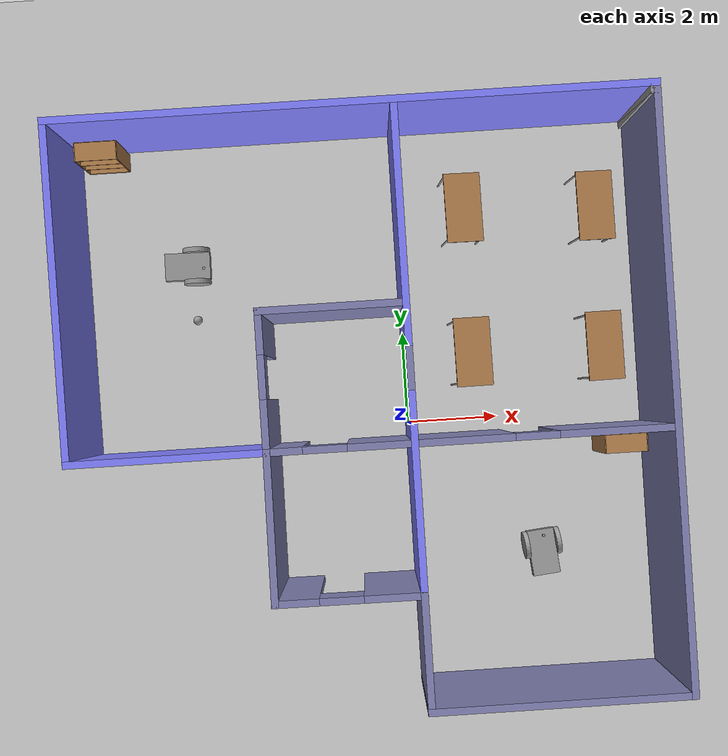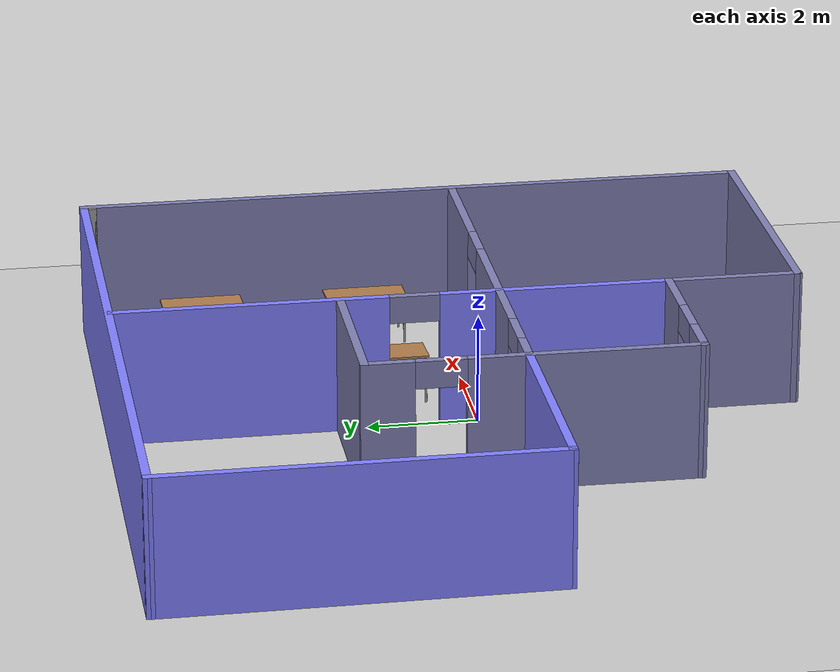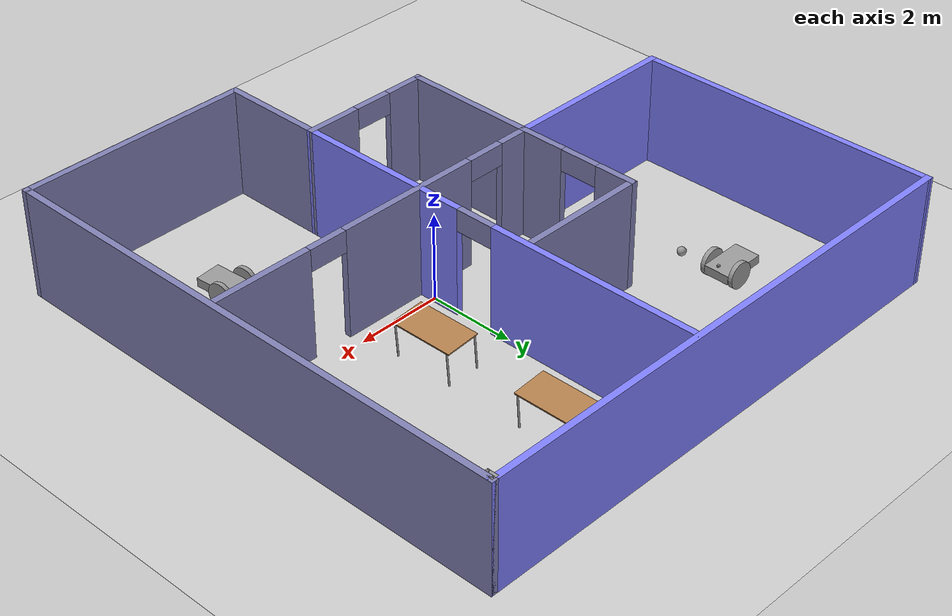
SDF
<sdf version="1.7">
 <world name="default">
  <plugin name="robotPlugin" filename="librobotPlugin.so"/>
  <light name="sun" type="directional">
   <pose>0 0 10 0 -0 0</pose>
   <diffuse>0.8 0.8 0.8 1</diffuse>
   <specular>0.2 0.2 0.2 1</specular>
   <attenuation>
    <range>1000</range>
    <constant>0.9</constant>
    <linear>0.01</linear>
    <quadratic>0.001</quadratic>
   </attenuation>
   <direction>-0.5 0.1 -0.9</direction>
   <spot><inner_angle>0</inner_angle><outer_angle>0</outer_angle><falloff>0</falloff></spot>
  </light>
  <model name="ground_plane">
   <static>1</static>
   <link name="link">
    <collision name="collision">
     <geometry><plane><normal>0 0 1</normal><size>100 100</size></plane></geometry>
     <surface>
      <contact><collide_bitmask>65535</collide_bitmask></contact>
      <friction><ode><mu>100</mu><mu2>50</mu2></ode></friction>
     </surface>
    </collision>
    <visual name="visual">
     <cast_shadows>0</cast_shadows>
     <geometry><plane><normal>0 0 1</normal><size>100 100</size></plane></geometry>
     <material>
      <script><uri>file://media/materials/scripts/gazebo.material</uri><name>Gazebo/Grey</name></script>
     </material>
    </visual>
   </link>
  </model>
  <gravity>0 0 -9.8</gravity>
  <magnetic_field>6e-06 2.3e-05 -4.2e-05</magnetic_field>
  <atmosphere type="adiabatic"/>
  <physics name="default_physics" default="0" type="ode">
   <max_step_size>0.001</max_step_size>
   <real_time_factor>1</real_time_factor>
   <real_time_update_rate>1000</real_time_update_rate>
  </physics>
  <scene><ambient>0.4 0.4 0.4 1</ambient><background>0.7 0.7 0.7 1</background><shadows>1</shadows></scene>
  <audio><device>default</device></audio>
  <spherical_coordinates>
   <surface_model>EARTH_WGS84</surface_model>
   <latitude_deg>0</latitude_deg>
   <longitude_deg>0</longitude_deg>
   <elevation>0</elevation>
   <heading_deg>0</heading_deg>
  </spherical_coordinates>
  <model name="table">
   <static>1</static>
   <link name="link">
    <collision name="surface">
     <pose>0 0 1 0 -0 0</pose>
     <geometry><box><size>1.5 0.8 0.03</size></box></geometry>
     <surface><friction><ode><mu>0.6</mu><mu2>0.6</mu2></ode></friction></surface>
    </collision>
    <visual name="visual1">
     <pose>0 0 1 0 -0 0</pose>
     <geometry><box><size>1.5 0.8 0.03</size></box></geometry>
     <material>
      <script><uri>file://media/materials/scripts/gazebo.material</uri><name>Gazebo/Wood</name></script>
     </material>
    </visual>
    <collision name="front_left_leg">
     <pose>0.68 0.38 0.5 0 -0 0</pose>
     <geometry><cylinder><radius>0.02</radius><length>1</length></cylinder></geometry>
    </collision>
    <visual name="front_left_leg">
     <pose>0.68 0.38 0.5 0 -0 0</pose>
     <geometry><cylinder><radius>0.02</radius><length>1</length></cylinder></geometry>
     <material>
      <script><uri>file://media/materials/scripts/gazebo.material</uri><name>Gazebo/Grey</name></script>
     </material>
    </visual>
    <collision name="front_right_leg">
     <pose>0.68 -0.38 0.5 0 -0 0</pose>
     <geometry><cylinder><radius>0.02</radius><length>1</length></cylinder></geometry>
    </collision>
    <visual name="front_right_leg">
     <pose>0.68 -0.38 0.5 0 -0 0</pose>
     <geometry><cylinder><radius>0.02</radius><length>1</length></cylinder></geometry>
     <material>
      <script><uri>file://media/materials/scripts/gazebo.material</uri><name>Gazebo/Grey</name></script>
     </material>
    </visual>
    <collision name="back_right_leg">
     <pose>-0.68 -0.38 0.5 0 -0 0</pose>
     <geometry><cylinder><radius>0.02</radius><length>1</length></cylinder></geometry>
    </collision>
    <visual name="back_right_leg">
     <pose>-0.68 -0.38 0.5 0 -0 0</pose>
     <geometry><cylinder><radius>0.02</radius><length>1</length></cylinder></geometry>
     <material>
      <script><uri>file://media/materials/scripts/gazebo.material</uri><name>Gazebo/Grey</name></script>
     </material>
    </visual>
    <collision name="back_left_leg">
     <pose>-0.68 0.38 0.5 0 -0 0</pose>
     <geometry><cylinder><radius>0.02</radius><length>1</length></cylinder></geometry>
    </collision>
    <visual name="back_left_leg">
     <pose>-0.68 0.38 0.5 0 -0 0</pose>
     <geometry><cylinder><radius>0.02</radius><length>1</length></cylinder></geometry>
     <material>
      <script><uri>file://media/materials/scripts/gazebo.material</uri><name>Gazebo/Grey</name></script>
     </material>
    </visual>
   </link>
   <pose>4.2736 4.48138 -0.182108 -0.078341 0.000521 -1.56416</pose>
  </model>
  <model name="table_clone">
   <static>1</static>
   <link name="link">
    <collision name="surface">
     <pose>0 0 1 0 -0 0</pose>
     <geometry><box><size>1.5 0.8 0.03</size></box></geometry>
     <surface><friction><ode><mu>0.6</mu><mu2>0.6</mu2></ode></friction></surface>
    </collision>
    <visual name="visual1">
     <pose>0 0 1 0 -0 0</pose>
     <geometry><box><size>1.5 0.8 0.03</size></box></geometry>
     <material>
      <script><uri>file://media/materials/scripts/gazebo.material</uri><name>Gazebo/Wood</name></script>
     </material>
    </visual>
    <collision name="front_left_leg">
     <pose>0.68 0.38 0.5 0 -0 0</pose>
     <geometry><cylinder><radius>0.02</radius><length>1</length></cylinder></geometry>
    </collision>
    <visual name="front_left_leg">
     <pose>0.68 0.38 0.5 0 -0 0</pose>
     <geometry><cylinder><radius>0.02</radius><length>1</length></cylinder></geometry>
     <material>
      <script><uri>file://media/materials/scripts/gazebo.material</uri><name>Gazebo/Grey</name></script>
     </material>
    </visual>
    <collision name="front_right_leg">
     <pose>0.68 -0.38 0.5 0 -0 0</pose>
     <geometry><cylinder><radius>0.02</radius><length>1</length></cylinder></geometry>
    </collision>
    <visual name="front_right_leg">
     <pose>0.68 -0.38 0.5 0 -0 0</pose>
     <geometry><cylinder><radius>0.02</radius><length>1</length></cylinder></geometry>
     <material>
      <script><uri>file://media/materials/scripts/gazebo.material</uri><name>Gazebo/Grey</name></script>
     </material>
    </visual>
    <collision name="back_right_leg">
     <pose>-0.68 -0.38 0.5 0 -0 0</pose>
     <geometry><cylinder><radius>0.02</radius><length>1</length></cylinder></geometry>
    </collision>
    <visual name="back_right_leg">
     <pose>-0.68 -0.38 0.5 0 -0 0</pose>
     <geometry><cylinder><radius>0.02</radius><length>1</length></cylinder></geometry>
     <material>
      <script><uri>file://media/materials/scripts/gazebo.material</uri><name>Gazebo/Grey</name></script>
     </material>
    </visual>
    <collision name="back_left_leg">
     <pose>-0.68 0.38 0.5 0 -0 0</pose>
     <geometry><cylinder><radius>0.02</radius><length>1</length></cylinder></geometry>
    </collision>
    <visual name="back_left_leg">
     <pose>-0.68 0.38 0.5 0 -0 0</pose>
     <geometry><cylinder><radius>0.02</radius><length>1</length></cylinder></geometry>
     <material>
      <script><uri>file://media/materials/scripts/gazebo.material</uri><name>Gazebo/Grey</name></script>
     </material>
    </visual>
   </link>
   <pose>1.39226 4.61245 -0.182108 -0.078341 0.000521 -1.56416</pose>
  </model>
  <model name="table_clone_0">
   <static>1</static>
   <link name="link">
    <collision name="surface">
     <pose>0 0 1 0 -0 0</pose>
     <geometry><box><size>1.5 0.8 0.03</size></box></geometry>
     <surface><friction><ode><mu>0.6</mu><mu2>0.6</mu2></ode></friction></surface>
    </collision>
    <visual name="visual1">
     <pose>0 0 1 0 -0 0</pose>
     <geometry><box><size>1.5 0.8 0.03</size></box></geometry>
     <material>
      <script><uri>file://media/materials/scripts/gazebo.material</uri><name>Gazebo/Wood</name></script>
     </material>
    </visual>
    <collision name="front_left_leg">
     <pose>0.68 0.38 0.5 0 -0 0</pose>
     <geometry><cylinder><radius>0.02</radius><length>1</length></cylinder></geometry>
    </collision>
    <visual name="front_left_leg">
     <pose>0.68 0.38 0.5 0 -0 0</pose>
     <geometry><cylinder><radius>0.02</radius><length>1</length></cylinder></geometry>
     <material>
      <script><uri>file://media/materials/scripts/gazebo.material</uri><name>Gazebo/Grey</name></script>
     </material>
    </visual>
    <collision name="front_right_leg">
     <pose>0.68 -0.38 0.5 0 -0 0</pose>
     <geometry><cylinder><radius>0.02</radius><length>1</length></cylinder></geometry>
    </collision>
    <visual name="front_right_leg">
     <pose>0.68 -0.38 0.5 0 -0 0</pose>
     <geometry><cylinder><radius>0.02</radius><length>1</length></cylinder></geometry>
     <material>
      <script><uri>file://media/materials/scripts/gazebo.material</uri><name>Gazebo/Grey</name></script>
     </material>
    </visual>
    <collision name="back_right_leg">
     <pose>-0.68 -0.38 0.5 0 -0 0</pose>
     <geometry><cylinder><radius>0.02</radius><length>1</length></cylinder></geometry>
    </collision>
    <visual name="back_right_leg">
     <pose>-0.68 -0.38 0.5 0 -0 0</pose>
     <geometry><cylinder><radius>0.02</radius><length>1</length></cylinder></geometry>
     <material>
      <script><uri>file://media/materials/scripts/gazebo.material</uri><name>Gazebo/Grey</name></script>
     </material>
    </visual>
    <collision name="back_left_leg">
     <pose>-0.68 0.38 0.5 0 -0 0</pose>
     <geometry><cylinder><radius>0.02</radius><length>1</length></cylinder></geometry>
    </collision>
    <visual name="back_left_leg">
     <pose>-0.68 0.38 0.5 0 -0 0</pose>
     <geometry><cylinder><radius>0.02</radius><length>1</length></cylinder></geometry>
     <material>
      <script><uri>file://media/materials/scripts/gazebo.material</uri><name>Gazebo/Grey</name></script>
     </material>
    </visual>
   </link>
   <pose>1.40873 1.45807 -0.182108 -0.078341 0.000521 -1.56416</pose>
  </model>
  <model name="table_clone_1">
   <static>1</static>
   <link name="link">
    <collision name="surface">
     <pose>0 0 1 0 -0 0</pose>
     <geometry><box><size>1.5 0.8 0.03</size></box></geometry>
     <surface><friction><ode><mu>0.6</mu><mu2>0.6</mu2></ode></friction></surface>
    </collision>
    <visual name="visual1">
     <pose>0 0 1 0 -0 0</pose>
     <geometry><box><size>1.5 0.8 0.03</size></box></geometry>
     <material>
      <script><uri>file://media/materials/scripts/gazebo.material</uri><name>Gazebo/Wood</name></script>
     </material>
    </visual>
    <collision name="front_left_leg">
     <pose>0.68 0.38 0.5 0 -0 0</pose>
     <geometry><cylinder><radius>0.02</radius><length>1</length></cylinder></geometry>
    </collision>
    <visual name="front_left_leg">
     <pose>0.68 0.38 0.5 0 -0 0</pose>
     <geometry><cylinder><radius>0.02</radius><length>1</length></cylinder></geometry>
     <material>
      <script><uri>file://media/materials/scripts/gazebo.material</uri><name>Gazebo/Grey</name></script>
     </material>
    </visual>
    <collision name="front_right_leg">
     <pose>0.68 -0.38 0.5 0 -0 0</pose>
     <geometry><cylinder><radius>0.02</radius><length>1</length></cylinder></geometry>
    </collision>
    <visual name="front_right_leg">
     <pose>0.68 -0.38 0.5 0 -0 0</pose>
     <geometry><cylinder><radius>0.02</radius><length>1</length></cylinder></geometry>
     <material>
      <script><uri>file://media/materials/scripts/gazebo.material</uri><name>Gazebo/Grey</name></script>
     </material>
    </visual>
    <collision name="back_right_leg">
     <pose>-0.68 -0.38 0.5 0 -0 0</pose>
     <geometry><cylinder><radius>0.02</radius><length>1</length></cylinder></geometry>
    </collision>
    <visual name="back_right_leg">
     <pose>-0.68 -0.38 0.5 0 -0 0</pose>
     <geometry><cylinder><radius>0.02</radius><length>1</length></cylinder></geometry>
     <material>
      <script><uri>file://media/materials/scripts/gazebo.material</uri><name>Gazebo/Grey</name></script>
     </material>
    </visual>
    <collision name="back_left_leg">
     <pose>-0.68 0.38 0.5 0 -0 0</pose>
     <geometry><cylinder><radius>0.02</radius><length>1</length></cylinder></geometry>
    </collision>
    <visual name="back_left_leg">
     <pose>-0.68 0.38 0.5 0 -0 0</pose>
     <geometry><cylinder><radius>0.02</radius><length>1</length></cylinder></geometry>
     <material>
      <script><uri>file://media/materials/scripts/gazebo.material</uri><name>Gazebo/Grey</name></script>
     </material>
    </visual>
   </link>
   <pose>4.29106 1.41438 -0.182108 -0.078341 0.000521 -1.56416</pose>
  </model>
  <model name="bookshelf">
   <static>1</static>
   <link name="link">
    <inertial><mass>1</mass></inertial>
    <collision name="back">
     <pose>0 0.005 0.6 0 -0 0</pose>
     <geometry><box><size>0.9 0.01 1.2</size></box></geometry>
    </collision>
    <visual name="visual1">
     <pose>0 0.005 0.6 0 -0 0</pose>
     <geometry><box><size>0.9 0.01 1.2</size></box></geometry>
     <material>
      <script><uri>file://media/materials/scripts/gazebo.material</uri><name>Gazebo/Wood</name></script>
     </material>
    </visual>
    <collision name="left_side">
     <pose>0.45 -0.195 0.6 0 -0 0</pose>
     <geometry><box><size>0.02 0.4 1.2</size></box></geometry>
    </collision>
    <visual name="visual2">
     <pose>0.45 -0.195 0.6 0 -0 0</pose>
     <geometry><box><size>0.02 0.4 1.2</size></box></geometry>
     <material>
      <script><uri>file://media/materials/scripts/gazebo.material</uri><name>Gazebo/Wood</name></script>
     </material>
    </visual>
    <collision name="right_side">
     <pose>-0.45 -0.195 0.6 0 -0 0</pose>
     <geometry><box><size>0.02 0.4 1.2</size></box></geometry>
    </collision>
    <visual name="visual3">
     <pose>-0.45 -0.195 0.6 0 -0 0</pose>
     <geometry><box><size>0.02 0.4 1.2</size></box></geometry>
     <material>
      <script><uri>file://media/materials/scripts/gazebo.material</uri><name>Gazebo/Wood</name></script>
     </material>
    </visual>
    <collision name="bottom">
     <pose>0 -0.195 0.03 0 -0 0</pose>
     <geometry><box><size>0.88 0.4 0.06</size></box></geometry>
    </collision>
    <visual name="visual4">
     <pose>0 -0.195 0.03 0 -0 0</pose>
     <geometry><box><size>0.88 0.4 0.06</size></box></geometry>
     <material>
      <script><uri>file://media/materials/scripts/gazebo.material</uri><name>Gazebo/Wood</name></script>
     </material>
    </visual>
    <collision name="top">
     <pose>0 -0.195 1.19 0 -0 0</pose>
     <geometry><box><size>0.88 0.4 0.02</size></box></geometry>
    </collision>
    <visual name="visual5">
     <pose>0 -0.195 1.19 0 -0 0</pose>
     <geometry><box><size>0.88 0.4 0.02</size></box></geometry>
     <material>
      <script><uri>file://media/materials/scripts/gazebo.material</uri><name>Gazebo/Wood</name></script>
     </material>
    </visual>
    <collision name="low_shelf">
     <pose>0 -0.195 0.43 0 -0 0</pose>
     <geometry><box><size>0.88 0.4 0.02</size></box></geometry>
    </collision>
    <visual name="visual6">
     <pose>0 -0.195 0.43 0 -0 0</pose>
     <geometry><box><size>0.88 0.4 0.02</size></box></geometry>
     <material>
      <script><uri>file://media/materials/scripts/gazebo.material</uri><name>Gazebo/Wood</name></script>
     </material>
    </visual>
    <collision name="high_shelf">
     <pose>0 -0.195 0.8 0 -0 0</pose>
     <geometry><box><size>0.88 0.4 0.02</size></box></geometry>
    </collision>
    <visual name="visual7">
     <pose>0 -0.195 0.8 0 -0 0</pose>
     <geometry><box><size>0.88 0.4 0.02</size></box></geometry>
     <material>
      <script><uri>file://media/materials/scripts/gazebo.material</uri><name>Gazebo/Wood</name></script>
     </material>
    </visual>
   </link>
   <pose>-6.37527 6.44399 0 0 -0 0</pose>
  </model>
  <model name="bookshelf_0">
   <static>1</static>
   <link name="link">
    <inertial><mass>1</mass></inertial>
    <collision name="back">
     <pose>0 0.005 0.6 0 -0 0</pose>
     <geometry><box><size>0.9 0.01 1.2</size></box></geometry>
    </collision>
    <visual name="visual1">
     <pose>0 0.005 0.6 0 -0 0</pose>
     <geometry><box><size>0.9 0.01 1.2</size></box></geometry>
     <material>
      <script><uri>file://media/materials/scripts/gazebo.material</uri><name>Gazebo/Wood</name></script>
     </material>
    </visual>
    <collision name="left_side">
     <pose>0.45 -0.195 0.6 0 -0 0</pose>
     <geometry><box><size>0.02 0.4 1.2</size></box></geometry>
    </collision>
    <visual name="visual2">
     <pose>0.45 -0.195 0.6 0 -0 0</pose>
     <geometry><box><size>0.02 0.4 1.2</size></box></geometry>
     <material>
      <script><uri>file://media/materials/scripts/gazebo.material</uri><name>Gazebo/Wood</name></script>
     </material>
    </visual>
    <collision name="right_side">
     <pose>-0.45 -0.195 0.6 0 -0 0</pose>
     <geometry><box><size>0.02 0.4 1.2</size></box></geometry>
    </collision>
    <visual name="visual3">
     <pose>-0.45 -0.195 0.6 0 -0 0</pose>
     <geometry><box><size>0.02 0.4 1.2</size></box></geometry>
     <material>
      <script><uri>file://media/materials/scripts/gazebo.material</uri><name>Gazebo/Wood</name></script>
     </material>
    </visual>
    <collision name="bottom">
     <pose>0 -0.195 0.03 0 -0 0</pose>
     <geometry><box><size>0.88 0.4 0.06</size></box></geometry>
    </collision>
    <visual name="visual4">
     <pose>0 -0.195 0.03 0 -0 0</pose>
     <geometry><box><size>0.88 0.4 0.06</size></box></geometry>
     <material>
      <script><uri>file://media/materials/scripts/gazebo.material</uri><name>Gazebo/Wood</name></script>
     </material>
    </visual>
    <collision name="top">
     <pose>0 -0.195 1.19 0 -0 0</pose>
     <geometry><box><size>0.88 0.4 0.02</size></box></geometry>
    </collision>
    <visual name="visual5">
     <pose>0 -0.195 1.19 0 -0 0</pose>
     <geometry><box><size>0.88 0.4 0.02</size></box></geometry>
     <material>
      <script><uri>file://media/materials/scripts/gazebo.material</uri><name>Gazebo/Wood</name></script>
     </material>
    </visual>
    <collision name="low_shelf">
     <pose>0 -0.195 0.43 0 -0 0</pose>
     <geometry><box><size>0.88 0.4 0.02</size></box></geometry>
    </collision>
    <visual name="visual6">
     <pose>0 -0.195 0.43 0 -0 0</pose>
     <geometry><box><size>0.88 0.4 0.02</size></box></geometry>
     <material>
      <script><uri>file://media/materials/scripts/gazebo.material</uri><name>Gazebo/Wood</name></script>
     </material>
    </visual>
    <collision name="high_shelf">
     <pose>0 -0.195 0.8 0 -0 0</pose>
     <geometry><box><size>0.88 0.4 0.02</size></box></geometry>
    </collision>
    <visual name="visual7">
     <pose>0 -0.195 0.8 0 -0 0</pose>
     <geometry><box><size>0.88 0.4 0.02</size></box></geometry>
     <material>
      <script><uri>file://media/materials/scripts/gazebo.material</uri><name>Gazebo/Wood</name></script>
     </material>
    </visual>
   </link>
   <pose>4.60051 -0.525793 0 0 -0 0</pose>
  </model>
  <model name="mobile_robot">
   <link name="link">
    <inertial>
     <mass>1</mass>
     <inertia>
      <ixx>0.166667</ixx>
      <ixy>0</ixy>
      <ixz>0</ixz>
      <iyy>0.166667</iyy>
      <iyz>0</iyz>
      <izz>0.166667</izz>
     </inertia>
    </inertial>
    <visual name="visual">
     <geometry><box><size>1 0.6 0.2</size></box></geometry>
     <material>
      <script><name>Gazebo/Grey</name><uri>file://media/materials/scripts/gazebo.material</uri></script>
      <shader type="vertex"><normal_map>__default__</normal_map></shader>
      <ambient>0.3 0.3 0.3 1</ambient>
      <diffuse>0.7 0.7 0.7 1</diffuse>
      <specular>0.01 0.01 0.01 1</specular>
      <emissive>0 0 0 1</emissive>
     </material>
    </visual>
    <collision name="collision">
     <geometry><box><size>1 0.6 0.2</size></box></geometry>
     <surface>
      <friction>
       <ode><mu>1</mu><mu2>1</mu2><fdir1>0 0 0</fdir1><slip1>0</slip1><slip2>0</slip2></ode>
       <torsional>
        <coefficient>1</coefficient>
        <patch_radius>0</patch_radius>
        <surface_radius>0</surface_radius>
        <use_patch_radius>1</use_patch_radius>
        <ode><slip>0</slip></ode>
       </torsional>
      </friction>
      <bounce><restitution_coefficient>0</restitution_coefficient><threshold>1e+06</threshold></bounce>
      <contact>
       <collide_without_contact>0</collide_without_contact>
       <collide_without_contact_bitmask>1</collide_without_contact_bitmask>
       <collide_bitmask>1</collide_bitmask>
       <ode>
        <soft_cfm>0</soft_cfm>
        <soft_erp>0.2</soft_erp>
        <kp>1e+13</kp>
        <kd>1</kd>
        <max_vel>0.01</max_vel>
        <min_depth>0</min_depth>
       </ode>
       <bullet>
        <split_impulse>1</split_impulse>
        <split_impulse_penetration_threshold>-0.01</split_impulse_penetration_threshold>
        <soft_cfm>0</soft_cfm>
        <soft_erp>0.2</soft_erp>
        <kp>1e+13</kp>
        <kd>1</kd>
       </bullet>
      </contact>
     </surface>
    </collision>
   </link>
   <link name="link_1">
    <inertial>
     <mass>1</mass>
     <inertia><ixx>0.145833</ixx><ixy>0</ixy><ixz>0</ixz><iyy>0.145833</iyy><iyz>0</iyz><izz>0.125</izz></inertia>
    </inertial>
    <pose>0.2 -0.350027 0.02 1.5707 -0 0</pose>
    <visual name="visual">
     <geometry><cylinder><radius>0.3</radius><length>0.1</length></cylinder></geometry>
     <material>
      <lighting>1</lighting>
      <script><uri>file://media/materials/scripts/gazebo.material</uri><name>Gazebo/Grey</name></script>
      <shader type="vertex"><normal_map>__default__</normal_map></shader>
      <ambient>0.3 0.3 0.3 1</ambient>
      <diffuse>0.7 0.7 0.7 1</diffuse>
      <specular>0.01 0.01 0.01 1</specular>
      <emissive>0 0 0 1</emissive>
     </material>
    </visual>
    <collision name="collision">
     <geometry><cylinder><radius>0.3</radius><length>0.1</length></cylinder></geometry>
     <surface>
      <friction>
       <ode><mu>1</mu><mu2>1</mu2><fdir1>0 0 0</fdir1><slip1>0</slip1><slip2>0</slip2></ode>
       <torsional>
        <coefficient>1</coefficient>
        <patch_radius>0</patch_radius>
        <surface_radius>0</surface_radius>
        <use_patch_radius>1</use_patch_radius>
        <ode><slip>0</slip></ode>
       </torsional>
      </friction>
      <bounce><restitution_coefficient>0</restitution_coefficient><threshold>1e+06</threshold></bounce>
      <contact>
       <collide_without_contact>0</collide_without_contact>
       <collide_without_contact_bitmask>1</collide_without_contact_bitmask>
       <collide_bitmask>1</collide_bitmask>
       <ode>
        <soft_cfm>0</soft_cfm>
        <soft_erp>0.2</soft_erp>
        <kp>1e+13</kp>
        <kd>1</kd>
        <max_vel>0.01</max_vel>
        <min_depth>0</min_depth>
       </ode>
       <bullet>
        <split_impulse>1</split_impulse>
        <split_impulse_penetration_threshold>-0.01</split_impulse_penetration_threshold>
        <soft_cfm>0</soft_cfm>
        <soft_erp>0.2</soft_erp>
        <kp>1e+13</kp>
        <kd>1</kd>
       </bullet>
      </contact>
     </surface>
    </collision>
   </link>
   <link name="link_1_clone">
    <inertial>
     <mass>1</mass>
     <inertia><ixx>0.145833</ixx><ixy>0</ixy><ixz>0</ixz><iyy>0.145833</iyy><iyz>0</iyz><izz>0.125</izz></inertia>
    </inertial>
    <pose>0.2 0.35003 0.019997 1.57069 -0 0</pose>
    <visual name="visual">
     <geometry><cylinder><radius>0.3</radius><length>0.1</length></cylinder></geometry>
     <material>
      <lighting>1</lighting>
      <script><uri>file://media/materials/scripts/gazebo.material</uri><name>Gazebo/Grey</name></script>
      <shader type="vertex"><normal_map>__default__</normal_map></shader>
      <ambient>0.3 0.3 0.3 1</ambient>
      <diffuse>0.7 0.7 0.7 1</diffuse>
      <specular>0.01 0.01 0.01 1</specular>
      <emissive>0 0 0 1</emissive>
     </material>
    </visual>
    <collision name="collision">
     <geometry><cylinder><radius>0.3</radius><length>0.1</length></cylinder></geometry>
     <surface>
      <friction>
       <ode><mu>1</mu><mu2>1</mu2><fdir1>0 0 0</fdir1><slip1>0</slip1><slip2>0</slip2></ode>
       <torsional>
        <coefficient>1</coefficient>
        <patch_radius>0</patch_radius>
        <surface_radius>0</surface_radius>
        <use_patch_radius>1</use_patch_radius>
        <ode><slip>0</slip></ode>
       </torsional>
      </friction>
      <bounce><restitution_coefficient>0</restitution_coefficient><threshold>1e+06</threshold></bounce>
      <contact>
       <collide_without_contact>0</collide_without_contact>
       <collide_without_contact_bitmask>1</collide_without_contact_bitmask>
       <collide_bitmask>1</collide_bitmask>
       <ode>
        <soft_cfm>0</soft_cfm>
        <soft_erp>0.2</soft_erp>
        <kp>1e+13</kp>
        <kd>1</kd>
        <max_vel>0.01</max_vel>
        <min_depth>0</min_depth>
       </ode>
       <bullet>
        <split_impulse>1</split_impulse>
        <split_impulse_penetration_threshold>-0.01</split_impulse_penetration_threshold>
        <soft_cfm>0</soft_cfm>
        <soft_erp>0.2</soft_erp>
        <kp>1e+13</kp>
        <kd>1</kd>
       </bullet>
      </contact>
     </surface>
    </collision>
   </link>
   <link name="link_2">
    <inertial>
     <mass>1</mass>
     <inertia><ixx>0.1</ixx><ixy>0</ixy><ixz>0</ixz><iyy>0.1</iyy><iyz>0</iyz><izz>0.1</izz></inertia>
    </inertial>
    <pose>-0.4 -0.020003 -0.2 -1e-05 -0 0</pose>
    <visual name="visual">
     <geometry><sphere><radius>0.1</radius></sphere></geometry>
     <material>
      <lighting>1</lighting>
      <script><uri>file://media/materials/scripts/gazebo.material</uri><name>Gazebo/Grey</name></script>
      <shader type="vertex"><normal_map>__default__</normal_map></shader>
      <ambient>0.3 0.3 0.3 1</ambient>
      <diffuse>0.7 0.7 0.7 1</diffuse>
      <specular>0.01 0.01 0.01 1</specular>
      <emissive>0 0 0 1</emissive>
     </material>
    </visual>
    <collision name="collision">
     <geometry><sphere><radius>0.1</radius></sphere></geometry>
     <surface>
      <friction>
       <ode><mu>1</mu><mu2>1</mu2><fdir1>0 0 0</fdir1><slip1>0</slip1><slip2>0</slip2></ode>
       <torsional>
        <coefficient>1</coefficient>
        <patch_radius>0</patch_radius>
        <surface_radius>0</surface_radius>
        <use_patch_radius>1</use_patch_radius>
        <ode><slip>0</slip></ode>
       </torsional>
      </friction>
      <bounce><restitution_coefficient>0</restitution_coefficient><threshold>1e+06</threshold></bounce>
      <contact>
       <collide_without_contact>0</collide_without_contact>
       <collide_without_contact_bitmask>1</collide_without_contact_bitmask>
       <collide_bitmask>1</collide_bitmask>
       <ode>
        <soft_cfm>0</soft_cfm>
        <soft_erp>0.2</soft_erp>
        <kp>1e+13</kp>
        <kd>1</kd>
        <max_vel>0.01</max_vel>
        <min_depth>0</min_depth>
       </ode>
       <bullet>
        <split_impulse>1</split_impulse>
        <split_impulse_penetration_threshold>-0.01</split_impulse_penetration_threshold>
        <soft_cfm>0</soft_cfm>
        <soft_erp>0.2</soft_erp>
        <kp>1e+13</kp>
        <kd>1</kd>
       </bullet>
      </contact>
     </surface>
    </collision>
   </link>
   <link name="link_3">
    <inertial>
     <mass>1</mass>
     <inertia>
      <ixx>0.166667</ixx>
      <ixy>0</ixy>
      <ixz>0</ixz>
      <iyy>0.166667</iyy>
      <iyz>0</iyz>
      <izz>0.166667</izz>
     </inertia>
    </inertial>
    <pose>0.360001 -0.057499 0.12 -1e-05 -0 0</pose>
    <visual name="visual">
     <geometry><box><size>0.05 0.05 0.05</size></box></geometry>
     <material>
      <lighting>1</lighting>
      <script><uri>file://media/materials/scripts/gazebo.material</uri><name>Gazebo/Grey</name></script>
      <shader type="vertex"><normal_map>__default__</normal_map></shader>
      <ambient>0.3 0.3 0.3 1</ambient>
      <diffuse>0.7 0.7 0.7 1</diffuse>
      <specular>0.01 0.01 0.01 1</specular>
      <emissive>0 0 0 1</emissive>
     </material>
    </visual>
    <collision name="collision">
     <geometry><box><size>0.05 0.05 0.05</size></box></geometry>
     <surface>
      <friction>
       <ode><mu>1</mu><mu2>1</mu2><fdir1>0 0 0</fdir1><slip1>0</slip1><slip2>0</slip2></ode>
       <torsional>
        <coefficient>1</coefficient>
        <patch_radius>0</patch_radius>
        <surface_radius>0</surface_radius>
        <use_patch_radius>1</use_patch_radius>
        <ode><slip>0</slip></ode>
       </torsional>
      </friction>
      <bounce><restitution_coefficient>0</restitution_coefficient><threshold>1e+06</threshold></bounce>
      <contact>
       <collide_without_contact>0</collide_without_contact>
       <collide_without_contact_bitmask>1</collide_without_contact_bitmask>
       <collide_bitmask>1</collide_bitmask>
       <ode>
        <soft_cfm>0</soft_cfm>
        <soft_erp>0.2</soft_erp>
        <kp>1e+13</kp>
        <kd>1</kd>
        <max_vel>0.01</max_vel>
        <min_depth>0</min_depth>
       </ode>
       <bullet>
        <split_impulse>1</split_impulse>
        <split_impulse_penetration_threshold>-0.01</split_impulse_penetration_threshold>
        <soft_cfm>0</soft_cfm>
        <soft_erp>0.2</soft_erp>
        <kp>1e+13</kp>
        <kd>1</kd>
       </bullet>
      </contact>
     </surface>
    </collision>
   </link>
   <joint name="link_JOINT_1" type="revolute">
    <parent>link</parent>
    <child>link_1</child>
    <axis>
     <xyz>0 0 -1</xyz>
     <limit>
      <lower>-1.79769e+308</lower>
      <upper>1.79769e+308</upper>
      <effort>-1</effort>
      <velocity>-1</velocity>
     </limit>
     <dynamics>
      <spring_reference>0</spring_reference>
      <spring_stiffness>0</spring_stiffness>
      <damping>0</damping>
      <friction>0</friction>
     </dynamics>
    </axis>
    <physics>
     <ode><limit><cfm>0</cfm><erp>0.2</erp></limit><suspension><cfm>0</cfm><erp>0.2</erp></suspension></ode>
    </physics>
   </joint>
   <joint name="link_JOINT_2" type="revolute">
    <parent>link</parent>
    <child>link_1_clone</child>
    <axis>
     <xyz>0 0 1</xyz>
     <limit>
      <lower>-1.79769e+308</lower>
      <upper>1.79769e+308</upper>
      <effort>-1</effort>
      <velocity>-1</velocity>
     </limit>
     <dynamics>
      <spring_reference>0</spring_reference>
      <spring_stiffness>0</spring_stiffness>
      <damping>0</damping>
     </dynamics>
    </axis>
    <physics>
     <ode><limit><cfm>0</cfm><erp>0.2</erp></limit><suspension><cfm>0</cfm><erp>0.2</erp></suspension></ode>
    </physics>
   </joint>
   <joint name="link_JOINT_3" type="ball">
    <parent>link</parent>
    <child>link_2</child>
    <physics>
     <ode><limit><cfm>0</cfm><erp>0.2</erp></limit><suspension><cfm>0</cfm><erp>0.2</erp></suspension></ode>
    </physics>
   </joint>
   <joint name="link_JOINT_4" type="fixed">
    <parent>link</parent>
    <child>link_3</child>
    <physics>
     <ode><limit><cfm>0</cfm><erp>0.2</erp></limit><suspension><cfm>0</cfm><erp>0.2</erp></suspension></ode>
    </physics>
   </joint>
   <static>0</static>
   <pose>2.81878 -3.07687 0.286642 5e-06 0.033128 1.67121</pose>
  </model>
  <model name="mobile_robot_0">
   <link name="link">
    <inertial>
     <mass>1</mass>
     <inertia>
      <ixx>0.166667</ixx>
      <ixy>0</ixy>
      <ixz>0</ixz>
      <iyy>0.166667</iyy>
      <iyz>0</iyz>
      <izz>0.166667</izz>
     </inertia>
    </inertial>
    <visual name="visual">
     <geometry><box><size>1 0.6 0.2</size></box></geometry>
     <material>
      <script><name>Gazebo/Grey</name><uri>file://media/materials/scripts/gazebo.material</uri></script>
      <shader type="vertex"><normal_map>__default__</normal_map></shader>
      <ambient>0.3 0.3 0.3 1</ambient>
      <diffuse>0.7 0.7 0.7 1</diffuse>
      <specular>0.01 0.01 0.01 1</specular>
      <emissive>0 0 0 1</emissive>
     </material>
    </visual>
    <collision name="collision">
     <geometry><box><size>1 0.6 0.2</size></box></geometry>
     <surface>
      <friction>
       <ode><mu>1</mu><mu2>1</mu2><fdir1>0 0 0</fdir1><slip1>0</slip1><slip2>0</slip2></ode>
       <torsional>
        <coefficient>1</coefficient>
        <patch_radius>0</patch_radius>
        <surface_radius>0</surface_radius>
        <use_patch_radius>1</use_patch_radius>
        <ode><slip>0</slip></ode>
       </torsional>
      </friction>
      <bounce><restitution_coefficient>0</restitution_coefficient><threshold>1e+06</threshold></bounce>
      <contact>
       <collide_without_contact>0</collide_without_contact>
       <collide_without_contact_bitmask>1</collide_without_contact_bitmask>
       <collide_bitmask>1</collide_bitmask>
       <ode>
        <soft_cfm>0</soft_cfm>
        <soft_erp>0.2</soft_erp>
        <kp>1e+13</kp>
        <kd>1</kd>
        <max_vel>0.01</max_vel>
        <min_depth>0</min_depth>
       </ode>
       <bullet>
        <split_impulse>1</split_impulse>
        <split_impulse_penetration_threshold>-0.01</split_impulse_penetration_threshold>
        <soft_cfm>0</soft_cfm>
        <soft_erp>0.2</soft_erp>
        <kp>1e+13</kp>
        <kd>1</kd>
       </bullet>
      </contact>
     </surface>
    </collision>
   </link>
   <link name="link_1">
    <inertial>
     <mass>1</mass>
     <inertia><ixx>0.145833</ixx><ixy>0</ixy><ixz>0</ixz><iyy>0.145833</iyy><iyz>0</iyz><izz>0.125</izz></inertia>
    </inertial>
    <pose>0.2 -0.350027 0.02 1.5707 -0 0</pose>
    <visual name="visual">
     <geometry><cylinder><radius>0.3</radius><length>0.1</length></cylinder></geometry>
     <material>
      <lighting>1</lighting>
      <script><uri>file://media/materials/scripts/gazebo.material</uri><name>Gazebo/Grey</name></script>
      <shader type="vertex"><normal_map>__default__</normal_map></shader>
      <ambient>0.3 0.3 0.3 1</ambient>
      <diffuse>0.7 0.7 0.7 1</diffuse>
      <specular>0.01 0.01 0.01 1</specular>
      <emissive>0 0 0 1</emissive>
     </material>
    </visual>
    <collision name="collision">
     <geometry><cylinder><radius>0.3</radius><length>0.1</length></cylinder></geometry>
     <surface>
      <friction>
       <ode><mu>1</mu><mu2>1</mu2><fdir1>0 0 0</fdir1><slip1>0</slip1><slip2>0</slip2></ode>
       <torsional>
        <coefficient>1</coefficient>
        <patch_radius>0</patch_radius>
        <surface_radius>0</surface_radius>
        <use_patch_radius>1</use_patch_radius>
        <ode><slip>0</slip></ode>
       </torsional>
      </friction>
      <bounce><restitution_coefficient>0</restitution_coefficient><threshold>1e+06</threshold></bounce>
      <contact>
       <collide_without_contact>0</collide_without_contact>
       <collide_without_contact_bitmask>1</collide_without_contact_bitmask>
       <collide_bitmask>1</collide_bitmask>
       <ode>
        <soft_cfm>0</soft_cfm>
        <soft_erp>0.2</soft_erp>
        <kp>1e+13</kp>
        <kd>1</kd>
        <max_vel>0.01</max_vel>
        <min_depth>0</min_depth>
       </ode>
       <bullet>
        <split_impulse>1</split_impulse>
        <split_impulse_penetration_threshold>-0.01</split_impulse_penetration_threshold>
        <soft_cfm>0</soft_cfm>
        <soft_erp>0.2</soft_erp>
        <kp>1e+13</kp>
        <kd>1</kd>
       </bullet>
      </contact>
     </surface>
    </collision>
   </link>
   <link name="link_1_clone">
    <inertial>
     <mass>1</mass>
     <inertia><ixx>0.145833</ixx><ixy>0</ixy><ixz>0</ixz><iyy>0.145833</iyy><iyz>0</iyz><izz>0.125</izz></inertia>
    </inertial>
    <pose>0.2 0.35003 0.019997 1.57069 -0 0</pose>
    <visual name="visual">
     <geometry><cylinder><radius>0.3</radius><length>0.1</length></cylinder></geometry>
     <material>
      <lighting>1</lighting>
      <script><uri>file://media/materials/scripts/gazebo.material</uri><name>Gazebo/Grey</name></script>
      <shader type="vertex"><normal_map>__default__</normal_map></shader>
      <ambient>0.3 0.3 0.3 1</ambient>
      <diffuse>0.7 0.7 0.7 1</diffuse>
      <specular>0.01 0.01 0.01 1</specular>
      <emissive>0 0 0 1</emissive>
     </material>
    </visual>
    <collision name="collision">
     <geometry><cylinder><radius>0.3</radius><length>0.1</length></cylinder></geometry>
     <surface>
      <friction>
       <ode><mu>1</mu><mu2>1</mu2><fdir1>0 0 0</fdir1><slip1>0</slip1><slip2>0</slip2></ode>
       <torsional>
        <coefficient>1</coefficient>
        <patch_radius>0</patch_radius>
        <surface_radius>0</surface_radius>
        <use_patch_radius>1</use_patch_radius>
        <ode><slip>0</slip></ode>
       </torsional>
      </friction>
      <bounce><restitution_coefficient>0</restitution_coefficient><threshold>1e+06</threshold></bounce>
      <contact>
       <collide_without_contact>0</collide_without_contact>
       <collide_without_contact_bitmask>1</collide_without_contact_bitmask>
       <collide_bitmask>1</collide_bitmask>
       <ode>
        <soft_cfm>0</soft_cfm>
        <soft_erp>0.2</soft_erp>
        <kp>1e+13</kp>
        <kd>1</kd>
        <max_vel>0.01</max_vel>
        <min_depth>0</min_depth>
       </ode>
       <bullet>
        <split_impulse>1</split_impulse>
        <split_impulse_penetration_threshold>-0.01</split_impulse_penetration_threshold>
        <soft_cfm>0</soft_cfm>
        <soft_erp>0.2</soft_erp>
        <kp>1e+13</kp>
        <kd>1</kd>
       </bullet>
      </contact>
     </surface>
    </collision>
   </link>
   <link name="link_2">
    <inertial>
     <mass>1</mass>
     <inertia><ixx>0.1</ixx><ixy>0</ixy><ixz>0</ixz><iyy>0.1</iyy><iyz>0</iyz><izz>0.1</izz></inertia>
    </inertial>
    <pose>-0.4 -0.020003 -0.2 -1e-05 -0 0</pose>
    <visual name="visual">
     <geometry><sphere><radius>0.1</radius></sphere></geometry>
     <material>
      <lighting>1</lighting>
      <script><uri>file://media/materials/scripts/gazebo.material</uri><name>Gazebo/Grey</name></script>
      <shader type="vertex"><normal_map>__default__</normal_map></shader>
      <ambient>0.3 0.3 0.3 1</ambient>
      <diffuse>0.7 0.7 0.7 1</diffuse>
      <specular>0.01 0.01 0.01 1</specular>
      <emissive>0 0 0 1</emissive>
     </material>
    </visual>
    <collision name="collision">
     <geometry><sphere><radius>0.1</radius></sphere></geometry>
     <surface>
      <friction>
       <ode><mu>1</mu><mu2>1</mu2><fdir1>0 0 0</fdir1><slip1>0</slip1><slip2>0</slip2></ode>
       <torsional>
        <coefficient>1</coefficient>
        <patch_radius>0</patch_radius>
        <surface_radius>0</surface_radius>
        <use_patch_radius>1</use_patch_radius>
        <ode><slip>0</slip></ode>
       </torsional>
      </friction>
      <bounce><restitution_coefficient>0</restitution_coefficient><threshold>1e+06</threshold></bounce>
      <contact>
       <collide_without_contact>0</collide_without_contact>
       <collide_without_contact_bitmask>1</collide_without_contact_bitmask>
       <collide_bitmask>1</collide_bitmask>
       <ode>
        <soft_cfm>0</soft_cfm>
        <soft_erp>0.2</soft_erp>
        <kp>1e+13</kp>
        <kd>1</kd>
        <max_vel>0.01</max_vel>
        <min_depth>0</min_depth>
       </ode>
       <bullet>
        <split_impulse>1</split_impulse>
        <split_impulse_penetration_threshold>-0.01</split_impulse_penetration_threshold>
        <soft_cfm>0</soft_cfm>
        <soft_erp>0.2</soft_erp>
        <kp>1e+13</kp>
        <kd>1</kd>
       </bullet>
      </contact>
     </surface>
    </collision>
   </link>
   <link name="link_3">
    <inertial>
     <mass>1</mass>
     <inertia>
      <ixx>0.166667</ixx>
      <ixy>0</ixy>
      <ixz>0</ixz>
      <iyy>0.166667</iyy>
      <iyz>0</iyz>
      <izz>0.166667</izz>
     </inertia>
    </inertial>
    <pose>0.360001 -0.057499 0.12 -1e-05 -0 0</pose>
    <visual name="visual">
     <geometry><box><size>0.05 0.05 0.05</size></box></geometry>
     <material>
      <lighting>1</lighting>
      <script><uri>file://media/materials/scripts/gazebo.material</uri><name>Gazebo/Grey</name></script>
      <shader type="vertex"><normal_map>__default__</normal_map></shader>
      <ambient>0.3 0.3 0.3 1</ambient>
      <diffuse>0.7 0.7 0.7 1</diffuse>
      <specular>0.01 0.01 0.01 1</specular>
      <emissive>0 0 0 1</emissive>
     </material>
    </visual>
    <collision name="collision">
     <geometry><box><size>0.05 0.05 0.05</size></box></geometry>
     <surface>
      <friction>
       <ode><mu>1</mu><mu2>1</mu2><fdir1>0 0 0</fdir1><slip1>0</slip1><slip2>0</slip2></ode>
       <torsional>
        <coefficient>1</coefficient>
        <patch_radius>0</patch_radius>
        <surface_radius>0</surface_radius>
        <use_patch_radius>1</use_patch_radius>
        <ode><slip>0</slip></ode>
       </torsional>
      </friction>
      <bounce><restitution_coefficient>0</restitution_coefficient><threshold>1e+06</threshold></bounce>
      <contact>
       <collide_without_contact>0</collide_without_contact>
       <collide_without_contact_bitmask>1</collide_without_contact_bitmask>
       <collide_bitmask>1</collide_bitmask>
       <ode>
        <soft_cfm>0</soft_cfm>
        <soft_erp>0.2</soft_erp>
        <kp>1e+13</kp>
        <kd>1</kd>
        <max_vel>0.01</max_vel>
        <min_depth>0</min_depth>
       </ode>
       <bullet>
        <split_impulse>1</split_impulse>
        <split_impulse_penetration_threshold>-0.01</split_impulse_penetration_threshold>
        <soft_cfm>0</soft_cfm>
        <soft_erp>0.2</soft_erp>
        <kp>1e+13</kp>
        <kd>1</kd>
       </bullet>
      </contact>
     </surface>
    </collision>
   </link>
   <joint name="link_JOINT_1" type="revolute">
    <parent>link</parent>
    <child>link_1</child>
    <axis>
     <xyz>0 0 -1</xyz>
     <limit>
      <lower>-1.79769e+308</lower>
      <upper>1.79769e+308</upper>
      <effort>-1</effort>
      <velocity>-1</velocity>
     </limit>
     <dynamics>
      <spring_reference>0</spring_reference>
      <spring_stiffness>0</spring_stiffness>
      <damping>0</damping>
      <friction>0</friction>
     </dynamics>
    </axis>
    <physics>
     <ode><limit><cfm>0</cfm><erp>0.2</erp></limit><suspension><cfm>0</cfm><erp>0.2</erp></suspension></ode>
    </physics>
   </joint>
   <joint name="link_JOINT_2" type="revolute">
    <parent>link</parent>
    <child>link_1_clone</child>
    <axis>
     <xyz>0 0 1</xyz>
     <limit>
      <lower>-1.79769e+308</lower>
      <upper>1.79769e+308</upper>
      <effort>-1</effort>
      <velocity>-1</velocity>
     </limit>
     <dynamics>
      <spring_reference>0</spring_reference>
      <spring_stiffness>0</spring_stiffness>
      <damping>0</damping>
     </dynamics>
    </axis>
    <physics>
     <ode><limit><cfm>0</cfm><erp>0.2</erp></limit><suspension><cfm>0</cfm><erp>0.2</erp></suspension></ode>
    </physics>
   </joint>
   <joint name="link_JOINT_3" type="ball">
    <parent>link</parent>
    <child>link_2</child>
    <physics>
     <ode><limit><cfm>0</cfm><erp>0.2</erp></limit><suspension><cfm>0</cfm><erp>0.2</erp></suspension></ode>
    </physics>
   </joint>
   <joint name="link_JOINT_4" type="fixed">
    <parent>link</parent>
    <child>link_3</child>
    <physics>
     <ode><limit><cfm>0</cfm><erp>0.2</erp></limit><suspension><cfm>0</cfm><erp>0.2</erp></suspension></ode>
    </physics>
   </joint>
   <static>0</static>
   <pose>-4.70023 3.77336 0.286642 5e-06 0.033128 -0.010384</pose>
  </model>
  <model name="white_ball">
   <link name="link_1">
    <inertial>
     <mass>1</mass>
     <inertia><ixx>0.1</ixx><ixy>0</ixy><ixz>0</ixz><iyy>0.1</iyy><iyz>0</iyz><izz>0.1</izz></inertia>
    </inertial>
    <pose>-0 -2e-06 -0 0 -0 0</pose>
    <visual name="visual">
     <geometry><sphere><radius>0.1</radius></sphere></geometry>
     <material>
      <lighting>1</lighting>
      <script><uri>file://media/materials/scripts/gazebo.material</uri><name>Gazebo/Grey</name></script>
      <shader type="pixel"><normal_map>__default__</normal_map></shader>
      <ambient>1 1 1 1</ambient>
      <diffuse>1 1 1 1</diffuse>
      <specular>1 1 1 1</specular>
      <emissive>0 0 0 1</emissive>
     </material>
    </visual>
    <collision name="collision">
     <geometry><sphere><radius>0.1</radius></sphere></geometry>
     <surface>
      <friction>
       <ode><mu>1</mu><mu2>1</mu2><fdir1>0 0 0</fdir1><slip1>0</slip1><slip2>0</slip2></ode>
       <torsional>
        <coefficient>1</coefficient>
        <patch_radius>0</patch_radius>
        <surface_radius>0</surface_radius>
        <use_patch_radius>1</use_patch_radius>
        <ode><slip>0</slip></ode>
       </torsional>
      </friction>
      <bounce><restitution_coefficient>0</restitution_coefficient><threshold>1e+06</threshold></bounce>
      <contact>
       <collide_without_contact>0</collide_without_contact>
       <collide_without_contact_bitmask>1</collide_without_contact_bitmask>
       <collide_bitmask>1</collide_bitmask>
       <ode>
        <soft_cfm>0</soft_cfm>
        <soft_erp>0.2</soft_erp>
        <kp>1e+13</kp>
        <kd>1</kd>
        <max_vel>0.01</max_vel>
        <min_depth>0</min_depth>
       </ode>
       <bullet>
        <split_impulse>1</split_impulse>
        <split_impulse_penetration_threshold>-0.01</split_impulse_penetration_threshold>
        <soft_cfm>0</soft_cfm>
        <soft_erp>0.2</soft_erp>
        <kp>1e+13</kp>
        <kd>1</kd>
       </bullet>
      </contact>
     </surface>
    </collision>
   </link>
   <static>0</static>
   <pose>-4.58796 2.58345 0.1 0 -0 0</pose>
  </model>
  <model name="robotBuilding">
   <link name="Wall_15">
    <pose>0.000176 6.17768 0 0 -0 0</pose>
    <inertial>
     <mass>1</mass>
     <inertia><ixx>1</ixx><ixy>0</ixy><ixz>0</ixz><iyy>1</iyy><iyz>0</iyz><izz>1</izz></inertia>
    </inertial>
    <visual name="Wall_15_Visual">
     <pose>0 0 1.25 0 -0 0</pose>
     <geometry><box><size>12.5304 0.15 2.5</size></box></geometry>
     <material>
      <script><uri>file://media/materials/scripts/gazebo.material</uri><name>Gazebo/Grey</name></script>
      <ambient>0.5 0.5 1 1</ambient>
      <shader type="pixel"><normal_map>__default__</normal_map></shader>
      <diffuse>0.7 0.7 0.7 1</diffuse>
      <specular>0.01 0.01 0.01 1</specular>
      <emissive>0 0 0 1</emissive>
     </material>
     <meta><layer>0</layer></meta>
    </visual>
    <collision name="Wall_15_Collision">
     <pose>0 0 1.25 0 -0 0</pose>
     <geometry><box><size>12.5304 0.15 2.5</size></box></geometry>
     <surface>
      <friction>
       <ode><mu>1</mu><mu2>1</mu2><fdir1>0 0 0</fdir1><slip1>0</slip1><slip2>0</slip2></ode>
       <torsional>
        <coefficient>1</coefficient>
        <patch_radius>0</patch_radius>
        <surface_radius>0</surface_radius>
        <use_patch_radius>1</use_patch_radius>
        <ode><slip>0</slip></ode>
       </torsional>
      </friction>
      <bounce><restitution_coefficient>0</restitution_coefficient><threshold>1e+06</threshold></bounce>
      <contact>
       <collide_without_contact>0</collide_without_contact>
       <collide_without_contact_bitmask>1</collide_without_contact_bitmask>
       <collide_bitmask>1</collide_bitmask>
       <ode>
        <soft_cfm>0</soft_cfm>
        <soft_erp>0.2</soft_erp>
        <kp>1e+13</kp>
        <kd>1</kd>
        <max_vel>0.01</max_vel>
        <min_depth>0</min_depth>
       </ode>
       <bullet>
        <split_impulse>1</split_impulse>
        <split_impulse_penetration_threshold>-0.01</split_impulse_penetration_threshold>
        <soft_cfm>0</soft_cfm>
        <soft_erp>0.2</soft_erp>
        <kp>1e+13</kp>
        <kd>1</kd>
       </bullet>
      </contact>
     </surface>
    </collision>
   </link>
   <link name="Wall_16">
    <pose>6.19039 0.002678 0 0 0 -1.5708</pose>
    <inertial>
     <mass>1</mass>
     <inertia><ixx>1</ixx><ixy>0</ixy><ixz>0</ixz><iyy>1</iyy><iyz>0</iyz><izz>1</izz></inertia>
    </inertial>
    <visual name="Wall_16_Visual">
     <pose>0 0 1.25 0 -0 0</pose>
     <geometry><box><size>12.5 0.15 2.5</size></box></geometry>
     <material>
      <script><uri>file://media/materials/scripts/gazebo.material</uri><name>Gazebo/Grey</name></script>
      <ambient>0.5 0.5 1 1</ambient>
      <shader type="pixel"><normal_map>__default__</normal_map></shader>
      <diffuse>0.5 0.5 0.7 1</diffuse>
      <specular>0.01 0.01 0.01 1</specular>
      <emissive>0 0 0 1</emissive>
     </material>
     <meta><layer>0</layer></meta>
    </visual>
    <collision name="Wall_16_Collision">
     <pose>0 0 1.25 0 -0 0</pose>
     <geometry><box><size>12.5 0.15 2.5</size></box></geometry>
     <surface>
      <friction>
       <ode><mu>1</mu><mu2>1</mu2><fdir1>0 0 0</fdir1><slip1>0</slip1><slip2>0</slip2></ode>
       <torsional>
        <coefficient>1</coefficient>
        <patch_radius>0</patch_radius>
        <surface_radius>0</surface_radius>
        <use_patch_radius>1</use_patch_radius>
        <ode><slip>0</slip></ode>
       </torsional>
      </friction>
      <bounce><restitution_coefficient>0</restitution_coefficient><threshold>1e+06</threshold></bounce>
      <contact>
       <collide_without_contact>0</collide_without_contact>
       <collide_without_contact_bitmask>1</collide_without_contact_bitmask>
       <collide_bitmask>1</collide_bitmask>
       <ode>
        <soft_cfm>0</soft_cfm>
        <soft_erp>0.2</soft_erp>
        <kp>1e+13</kp>
        <kd>1</kd>
        <max_vel>0.01</max_vel>
        <min_depth>0</min_depth>
       </ode>
       <bullet>
        <split_impulse>1</split_impulse>
        <split_impulse_penetration_threshold>-0.01</split_impulse_penetration_threshold>
        <soft_cfm>0</soft_cfm>
        <soft_erp>0.2</soft_erp>
        <kp>1e+13</kp>
        <kd>1</kd>
       </bullet>
      </contact>
     </surface>
    </collision>
   </link>
   <link name="Wall_18">
    <pose>3.53731 -6.1752 0 0 0 -3.14051</pose>
    <inertial>
     <mass>1</mass>
     <inertia><ixx>1</ixx><ixy>0</ixy><ixz>0</ixz><iyy>1</iyy><iyz>0</iyz><izz>1</izz></inertia>
    </inertial>
    <visual name="Wall_18_Visual">
     <pose>0 0 1.25 0 -0 0</pose>
     <geometry><box><size>5.45623 0.15 2.5</size></box></geometry>
     <material>
      <script><uri>file://media/materials/scripts/gazebo.material</uri><name>Gazebo/Grey</name></script>
      <ambient>0.5 0.5 1 1</ambient>
      <shader type="pixel"><normal_map>__default__</normal_map></shader>
      <diffuse>0.5 0.5 0.7 1</diffuse>
      <specular>0.01 0.01 0.01 1</specular>
      <emissive>0 0 0 1</emissive>
     </material>
     <meta><layer>0</layer></meta>
    </visual>
    <collision name="Wall_18_Collision">
     <pose>0 0 1.25 0 -0 0</pose>
     <geometry><box><size>5.45623 0.15 2.5</size></box></geometry>
     <surface>
      <friction>
       <ode><mu>1</mu><mu2>1</mu2><fdir1>0 0 0</fdir1><slip1>0</slip1><slip2>0</slip2></ode>
       <torsional>
        <coefficient>1</coefficient>
        <patch_radius>0</patch_radius>
        <surface_radius>0</surface_radius>
        <use_patch_radius>1</use_patch_radius>
        <ode><slip>0</slip></ode>
       </torsional>
      </friction>
      <bounce><restitution_coefficient>0</restitution_coefficient><threshold>1e+06</threshold></bounce>
      <contact>
       <collide_without_contact>0</collide_without_contact>
       <collide_without_contact_bitmask>1</collide_without_contact_bitmask>
       <collide_bitmask>1</collide_bitmask>
       <ode>
        <soft_cfm>0</soft_cfm>
        <soft_erp>0.2</soft_erp>
        <kp>1e+13</kp>
        <kd>1</kd>
        <max_vel>0.01</max_vel>
        <min_depth>0</min_depth>
       </ode>
       <bullet>
        <split_impulse>1</split_impulse>
        <split_impulse_penetration_threshold>-0.01</split_impulse_penetration_threshold>
        <soft_cfm>0</soft_cfm>
        <soft_erp>0.2</soft_erp>
        <kp>1e+13</kp>
        <kd>1</kd>
       </bullet>
      </contact>
     </surface>
    </collision>
   </link>
   <link name="Wall_19">
    <pose>0.884227 -5.00307 0 0 -0 1.5708</pose>
    <inertial>
     <mass>1</mass>
     <inertia><ixx>1</ixx><ixy>0</ixy><ixz>0</ixz><iyy>1</iyy><iyz>0</iyz><izz>1</izz></inertia>
    </inertial>
    <visual name="Wall_19_Visual">
     <pose>0 0 1.25 0 -0 0</pose>
     <geometry><box><size>2.5 0.15 2.5</size></box></geometry>
     <material>
      <script><uri>file://media/materials/scripts/gazebo.material</uri><name>Gazebo/Grey</name></script>
      <ambient>0.5 0.5 1 1</ambient>
      <shader type="pixel"><normal_map>__default__</normal_map></shader>
      <diffuse>0.5 0.5 0.7 1</diffuse>
      <specular>0.01 0.01 0.01 1</specular>
      <emissive>0 0 0 1</emissive>
     </material>
     <meta><layer>0</layer></meta>
    </visual>
    <collision name="Wall_19_Collision">
     <pose>0 0 1.25 0 -0 0</pose>
     <geometry><box><size>2.5 0.15 2.5</size></box></geometry>
     <surface>
      <friction>
       <ode><mu>1</mu><mu2>1</mu2><fdir1>0 0 0</fdir1><slip1>0</slip1><slip2>0</slip2></ode>
       <torsional>
        <coefficient>1</coefficient>
        <patch_radius>0</patch_radius>
        <surface_radius>0</surface_radius>
        <use_patch_radius>1</use_patch_radius>
        <ode><slip>0</slip></ode>
       </torsional>
      </friction>
      <bounce><restitution_coefficient>0</restitution_coefficient><threshold>1e+06</threshold></bounce>
      <contact>
       <collide_without_contact>0</collide_without_contact>
       <collide_without_contact_bitmask>1</collide_without_contact_bitmask>
       <collide_bitmask>1</collide_bitmask>
       <ode>
        <soft_cfm>0</soft_cfm>
        <soft_erp>0.2</soft_erp>
        <kp>1e+13</kp>
        <kd>1</kd>
        <max_vel>0.01</max_vel>
        <min_depth>0</min_depth>
       </ode>
       <bullet>
        <split_impulse>1</split_impulse>
        <split_impulse_penetration_threshold>-0.01</split_impulse_penetration_threshold>
        <soft_cfm>0</soft_cfm>
        <soft_erp>0.2</soft_erp>
        <kp>1e+13</kp>
        <kd>1</kd>
       </bullet>
      </contact>
     </surface>
    </collision>
   </link>
   <link name="Wall_20">
    <pose>-0.623281 -3.82262 0 0 -0 3.13798</pose>
    <inertial>
     <mass>1</mass>
     <inertia><ixx>1</ixx><ixy>0</ixy><ixz>0</ixz><iyy>1</iyy><iyz>0</iyz><izz>1</izz></inertia>
    </inertial>
    <visual name="Wall_20_Visual_0">
     <pose>-0.937035 0 1.25 0 -0 0</pose>
     <geometry><box><size>1.291 0.15 2.5</size></box></geometry>
     <material>
      <script><uri>file://media/materials/scripts/gazebo.material</uri><name>Gazebo/Grey</name></script>
      <ambient>0.5 0.5 1 1</ambient>
      <shader type="pixel"><normal_map>__default__</normal_map></shader>
      <diffuse>0.5 0.5 0.7 1</diffuse>
      <specular>0 0.01 0.01 1</specular>
      <emissive>0 0 0 1</emissive>
     </material>
     <meta><layer>0</layer></meta>
    </visual>
    <visual name="Wall_20_Visual_1">
     <pose>1.0955 0 1.25 0 -0 0</pose>
     <geometry><box><size>0.97407 0.15 2.5</size></box></geometry>
     <material>
      <script><uri>file://media/materials/scripts/gazebo.material</uri><name>Gazebo/Grey</name></script>
      <ambient>0.5 0.5 1 1</ambient>
      <shader type="pixel"><normal_map>__default__</normal_map></shader>
      <diffuse>0.5 0.5 0.7 1</diffuse>
      <specular>0.01 0.01 0.01 1</specular>
      <emissive>0 0 0 1</emissive>
     </material>
     <meta><layer>0</layer></meta>
    </visual>
    <visual name="Wall_20_Visual_2">
     <pose>0.158466 0 2.25 0 -0 0</pose>
     <geometry><box><size>0.9 0.15 0.5</size></box></geometry>
     <material>
      <script><uri>file://media/materials/scripts/gazebo.material</uri><name>Gazebo/Grey</name></script>
      <ambient>0.5 0.5 1 1</ambient>
      <shader type="pixel"><normal_map>__default__</normal_map></shader>
      <diffuse>0.5 0.5 0.7 1</diffuse>
      <specular>0.01 0.01 0.01 1</specular>
      <emissive>0 0 0 1</emissive>
     </material>
     <meta><layer>0</layer></meta>
    </visual>
    <collision name="Wall_20_Collision_0">
     <pose>-0.937035 0 1.25 0 -0 0</pose>
     <geometry><box><size>1.291 0.15 2.5</size></box></geometry>
     <surface>
      <friction>
       <ode><mu>1</mu><mu2>1</mu2><fdir1>0 0 0</fdir1><slip1>0</slip1><slip2>0</slip2></ode>
       <torsional>
        <coefficient>1</coefficient>
        <patch_radius>0</patch_radius>
        <surface_radius>0</surface_radius>
        <use_patch_radius>1</use_patch_radius>
        <ode><slip>0</slip></ode>
       </torsional>
      </friction>
      <bounce><restitution_coefficient>0</restitution_coefficient><threshold>1e+06</threshold></bounce>
      <contact>
       <collide_without_contact>0</collide_without_contact>
       <collide_without_contact_bitmask>1</collide_without_contact_bitmask>
       <collide_bitmask>1</collide_bitmask>
       <ode>
        <soft_cfm>0</soft_cfm>
        <soft_erp>0.2</soft_erp>
        <kp>1e+13</kp>
        <kd>1</kd>
        <max_vel>0.01</max_vel>
        <min_depth>0</min_depth>
       </ode>
       <bullet>
        <split_impulse>1</split_impulse>
        <split_impulse_penetration_threshold>-0.01</split_impulse_penetration_threshold>
        <soft_cfm>0</soft_cfm>
        <soft_erp>0.2</soft_erp>
        <kp>1e+13</kp>
        <kd>1</kd>
       </bullet>
      </contact>
     </surface>
    </collision>
    <collision name="Wall_20_Collision_1">
     <pose>1.0955 0 1.25 0 -0 0</pose>
     <geometry><box><size>0.97407 0.15 2.5</size></box></geometry>
     <surface>
      <friction>
       <ode><mu>1</mu><mu2>1</mu2><fdir1>0 0 0</fdir1><slip1>0</slip1><slip2>0</slip2></ode>
       <torsional>
        <coefficient>1</coefficient>
        <patch_radius>0</patch_radius>
        <surface_radius>0</surface_radius>
        <use_patch_radius>1</use_patch_radius>
        <ode><slip>0</slip></ode>
       </torsional>
      </friction>
      <bounce><restitution_coefficient>0</restitution_coefficient><threshold>1e+06</threshold></bounce>
      <contact>
       <collide_without_contact>0</collide_without_contact>
       <collide_without_contact_bitmask>1</collide_without_contact_bitmask>
       <collide_bitmask>1</collide_bitmask>
       <ode>
        <soft_cfm>0</soft_cfm>
        <soft_erp>0.2</soft_erp>
        <kp>1e+13</kp>
        <kd>1</kd>
        <max_vel>0.01</max_vel>
        <min_depth>0</min_depth>
       </ode>
       <bullet>
        <split_impulse>1</split_impulse>
        <split_impulse_penetration_threshold>-0.01</split_impulse_penetration_threshold>
        <soft_cfm>0</soft_cfm>
        <soft_erp>0.2</soft_erp>
        <kp>1e+13</kp>
        <kd>1</kd>
       </bullet>
      </contact>
     </surface>
    </collision>
    <collision name="Wall_20_Collision_2">
     <pose>0.158466 0 2.25 0 -0 0</pose>
     <geometry><box><size>0.9 0.15 0.5</size></box></geometry>
     <surface>
      <friction>
       <ode><mu>1</mu><mu2>1</mu2><fdir1>0 0 0</fdir1><slip1>0</slip1><slip2>0</slip2></ode>
       <torsional>
        <coefficient>1</coefficient>
        <patch_radius>0</patch_radius>
        <surface_radius>0</surface_radius>
        <use_patch_radius>1</use_patch_radius>
        <ode><slip>0</slip></ode>
       </torsional>
      </friction>
      <bounce><restitution_coefficient>0</restitution_coefficient><threshold>1e+06</threshold></bounce>
      <contact>
       <collide_without_contact>0</collide_without_contact>
       <collide_without_contact_bitmask>1</collide_without_contact_bitmask>
       <collide_bitmask>1</collide_bitmask>
       <ode>
        <soft_cfm>0</soft_cfm>
        <soft_erp>0.2</soft_erp>
        <kp>1e+13</kp>
        <kd>1</kd>
        <max_vel>0.01</max_vel>
        <min_depth>0</min_depth>
       </ode>
       <bullet>
        <split_impulse>1</split_impulse>
        <split_impulse_penetration_threshold>-0.01</split_impulse_penetration_threshold>
        <soft_cfm>0</soft_cfm>
        <soft_erp>0.2</soft_erp>
        <kp>1e+13</kp>
        <kd>1</kd>
       </bullet>
      </contact>
     </surface>
    </collision>
   </link>
   <link name="Wall_21">
    <pose>-2.12004 -2.28807 0 0 -0 1.56377</pose>
    <inertial>
     <mass>1</mass>
     <inertia><ixx>1</ixx><ixy>0</ixy><ixz>0</ixz><iyy>1</iyy><iyz>0</iyz><izz>1</izz></inertia>
    </inertial>
    <visual name="Wall_21_Visual">
     <pose>0 0 1.25 0 -0 0</pose>
     <geometry><box><size>3.2083 0.15 2.5</size></box></geometry>
     <material>
      <script><uri>file://media/materials/scripts/gazebo.material</uri><name>Gazebo/Grey</name></script>
      <ambient>0.5 0.5 1 1</ambient>
      <shader type="pixel"><normal_map>__default__</normal_map></shader>
      <diffuse>0.5 0.5 0.7 1</diffuse>
      <specular>0.01 0.01 0.01 1</specular>
      <emissive>0 0 0 1</emissive>
     </material>
     <meta><layer>0</layer></meta>
    </visual>
    <collision name="Wall_21_Collision">
     <pose>0 0 1.25 0 -0 0</pose>
     <geometry><box><size>3.2083 0.15 2.5</size></box></geometry>
     <surface>
      <friction>
       <ode><mu>1</mu><mu2>1</mu2><fdir1>0 0 0</fdir1><slip1>0</slip1><slip2>0</slip2></ode>
       <torsional>
        <coefficient>1</coefficient>
        <patch_radius>0</patch_radius>
        <surface_radius>0</surface_radius>
        <use_patch_radius>1</use_patch_radius>
        <ode><slip>0</slip></ode>
       </torsional>
      </friction>
      <bounce><restitution_coefficient>0</restitution_coefficient><threshold>1e+06</threshold></bounce>
      <contact>
       <collide_without_contact>0</collide_without_contact>
       <collide_without_contact_bitmask>1</collide_without_contact_bitmask>
       <collide_bitmask>1</collide_bitmask>
       <ode>
        <soft_cfm>0</soft_cfm>
        <soft_erp>0.2</soft_erp>
        <kp>1e+13</kp>
        <kd>1</kd>
        <max_vel>0.01</max_vel>
        <min_depth>0</min_depth>
       </ode>
       <bullet>
        <split_impulse>1</split_impulse>
        <split_impulse_penetration_threshold>-0.01</split_impulse_penetration_threshold>
        <soft_cfm>0</soft_cfm>
        <soft_erp>0.2</soft_erp>
        <kp>1e+13</kp>
        <kd>1</kd>
       </bullet>
      </contact>
     </surface>
    </collision>
   </link>
   <link name="Wall_22">
    <pose>-4.12787 -0.758956 0 0 -0 3.14159</pose>
    <inertial>
     <mass>1</mass>
     <inertia><ixx>1</ixx><ixy>0</ixy><ixz>0</ixz><iyy>1</iyy><iyz>0</iyz><izz>1</izz></inertia>
    </inertial>
    <visual name="Wall_22_Visual">
     <pose>0 0 1.25 0 -0 0</pose>
     <geometry><box><size>4.18715 0.15 2.5</size></box></geometry>
     <material>
      <script><uri>file://media/materials/scripts/gazebo.material</uri><name>Gazebo/Grey</name></script>
      <ambient>0.5 0.5 1 1</ambient>
      <shader type="pixel"><normal_map>__default__</normal_map></shader>
      <diffuse>0.7 0.7 0.7 1</diffuse>
      <specular>0.01 0.01 0.01 1</specular>
      <emissive>0 0 0 1</emissive>
     </material>
     <meta><layer>0</layer></meta>
    </visual>
    <collision name="Wall_22_Collision">
     <pose>0 0 1.25 0 -0 0</pose>
     <geometry><box><size>4.18715 0.15 2.5</size></box></geometry>
     <surface>
      <friction>
       <ode><mu>1</mu><mu2>1</mu2><fdir1>0 0 0</fdir1><slip1>0</slip1><slip2>0</slip2></ode>
       <torsional>
        <coefficient>1</coefficient>
        <patch_radius>0</patch_radius>
        <surface_radius>0</surface_radius>
        <use_patch_radius>1</use_patch_radius>
        <ode><slip>0</slip></ode>
       </torsional>
      </friction>
      <bounce><restitution_coefficient>0</restitution_coefficient><threshold>1e+06</threshold></bounce>
      <contact>
       <collide_without_contact>0</collide_without_contact>
       <collide_without_contact_bitmask>1</collide_without_contact_bitmask>
       <collide_bitmask>1</collide_bitmask>
       <ode>
        <soft_cfm>0</soft_cfm>
        <soft_erp>0.2</soft_erp>
        <kp>1e+13</kp>
        <kd>1</kd>
        <max_vel>0.01</max_vel>
        <min_depth>0</min_depth>
       </ode>
       <bullet>
        <split_impulse>1</split_impulse>
        <split_impulse_penetration_threshold>-0.01</split_impulse_penetration_threshold>
        <soft_cfm>0</soft_cfm>
        <soft_erp>0.2</soft_erp>
        <kp>1e+13</kp>
        <kd>1</kd>
       </bullet>
      </contact>
     </surface>
    </collision>
   </link>
   <link name="Wall_23">
    <pose>-6.16824 2.70936 0 0 -0 1.57708</pose>
    <inertial>
     <mass>1</mass>
     <inertia><ixx>1</ixx><ixy>0</ixy><ixz>0</ixz><iyy>1</iyy><iyz>0</iyz><izz>1</izz></inertia>
    </inertial>
    <visual name="Wall_23_Visual">
     <pose>0 0 1.25 0 -0 0</pose>
     <geometry><box><size>7.08677 0.15 2.5</size></box></geometry>
     <material>
      <script><uri>file://media/materials/scripts/gazebo.material</uri><name>Gazebo/Grey</name></script>
      <ambient>0.5 0.5 1 1</ambient>
      <shader type="pixel"><normal_map>__default__</normal_map></shader>
      <diffuse>0.7 0.7 0.7 1</diffuse>
      <specular>0.01 0.01 0.01 1</specular>
      <emissive>0 0 0 1</emissive>
     </material>
     <meta><layer>0</layer></meta>
    </visual>
    <collision name="Wall_23_Collision">
     <pose>0 0 1.25 0 -0 0</pose>
     <geometry><box><size>7.08677 0.15 2.5</size></box></geometry>
     <surface>
      <friction>
       <ode><mu>1</mu><mu2>1</mu2><fdir1>0 0 0</fdir1><slip1>0</slip1><slip2>0</slip2></ode>
       <torsional>
        <coefficient>1</coefficient>
        <patch_radius>0</patch_radius>
        <surface_radius>0</surface_radius>
        <use_patch_radius>1</use_patch_radius>
        <ode><slip>0</slip></ode>
       </torsional>
      </friction>
      <bounce><restitution_coefficient>0</restitution_coefficient><threshold>1e+06</threshold></bounce>
      <contact>
       <collide_without_contact>0</collide_without_contact>
       <collide_without_contact_bitmask>1</collide_without_contact_bitmask>
       <collide_bitmask>1</collide_bitmask>
       <ode>
        <soft_cfm>0</soft_cfm>
        <soft_erp>0.2</soft_erp>
        <kp>1e+13</kp>
        <kd>1</kd>
        <max_vel>0.01</max_vel>
        <min_depth>0</min_depth>
       </ode>
       <bullet>
        <split_impulse>1</split_impulse>
        <split_impulse_penetration_threshold>-0.01</split_impulse_penetration_threshold>
        <soft_cfm>0</soft_cfm>
        <soft_erp>0.2</soft_erp>
        <kp>1e+13</kp>
        <kd>1</kd>
       </bullet>
      </contact>
     </surface>
    </collision>
   </link>
   <link name="Wall_26">
    <pose>0.884227 1.14693 0 0 -0 1.5708</pose>
    <inertial>
     <mass>1</mass>
     <inertia><ixx>1</ixx><ixy>0</ixy><ixz>0</ixz><iyy>1</iyy><iyz>0</iyz><izz>1</izz></inertia>
    </inertial>
    <visual name="Wall_26_Visual_0">
     <pose>-2.94215 0 1.25 0 -0 0</pose>
     <geometry><box><size>4.2157 0.15 2.5</size></box></geometry>
     <material>
      <script><uri>file://media/materials/scripts/gazebo.material</uri><name>Gazebo/Grey</name></script>
      <ambient>0.5 0.5 1 1</ambient>
      <shader type="pixel"><normal_map>__default__</normal_map></shader>
      <diffuse>0.7 0.7 0.7 1</diffuse>
      <specular>0.01 0.01 0.01 1</specular>
      <emissive>0 0 0 1</emissive>
     </material>
     <meta><layer>0</layer></meta>
    </visual>
    <visual name="Wall_26_Visual_1">
     <pose>2.55785 0 1.25 0 -0 0</pose>
     <geometry><box><size>4.9843 0.15 2.5</size></box></geometry>
     <material>
      <script><uri>file://media/materials/scripts/gazebo.material</uri><name>Gazebo/Grey</name></script>
      <ambient>0.5 0.5 1 1</ambient>
      <shader type="pixel"><normal_map>__default__</normal_map></shader>
      <diffuse>0.7 0.7 0.7 1</diffuse>
      <specular>0.01 0.01 0.01 1</specular>
      <emissive>0 0 0 1</emissive>
     </material>
     <meta><layer>0</layer></meta>
    </visual>
    <visual name="Wall_26_Visual_2">
     <pose>-0.384305 0 2.25 0 -0 0</pose>
     <geometry><box><size>0.9 0.15 0.5</size></box></geometry>
     <material>
      <script><uri>file://media/materials/scripts/gazebo.material</uri><name>Gazebo/Grey</name></script>
      <ambient>0.5 0.5 1 1</ambient>
      <shader type="pixel"><normal_map>__default__</normal_map></shader>
      <diffuse>0.5 0.5 0.7 1</diffuse>
      <specular>0.01 0.01 0.01 1</specular>
      <emissive>0 0 0 1</emissive>
     </material>
     <meta><layer>0</layer></meta>
    </visual>
    <collision name="Wall_26_Collision_0">
     <pose>-2.94215 0 1.25 0 -0 0</pose>
     <geometry><box><size>4.2157 0.15 2.5</size></box></geometry>
     <surface>
      <friction>
       <ode><mu>1</mu><mu2>1</mu2><fdir1>0 0 0</fdir1><slip1>0</slip1><slip2>0</slip2></ode>
       <torsional>
        <coefficient>1</coefficient>
        <patch_radius>0</patch_radius>
        <surface_radius>0</surface_radius>
        <use_patch_radius>1</use_patch_radius>
        <ode><slip>0</slip></ode>
       </torsional>
      </friction>
      <bounce><restitution_coefficient>0</restitution_coefficient><threshold>1e+06</threshold></bounce>
      <contact>
       <collide_without_contact>0</collide_without_contact>
       <collide_without_contact_bitmask>1</collide_without_contact_bitmask>
       <collide_bitmask>1</collide_bitmask>
       <ode>
        <soft_cfm>0</soft_cfm>
        <soft_erp>0.2</soft_erp>
        <kp>1e+13</kp>
        <kd>1</kd>
        <max_vel>0.01</max_vel>
        <min_depth>0</min_depth>
       </ode>
       <bullet>
        <split_impulse>1</split_impulse>
        <split_impulse_penetration_threshold>-0.01</split_impulse_penetration_threshold>
        <soft_cfm>0</soft_cfm>
        <soft_erp>0.2</soft_erp>
        <kp>1e+13</kp>
        <kd>1</kd>
       </bullet>
      </contact>
     </surface>
    </collision>
    <collision name="Wall_26_Collision_1">
     <pose>2.55785 0 1.25 0 -0 0</pose>
     <geometry><box><size>4.9843 0.15 2.5</size></box></geometry>
     <surface>
      <friction>
       <ode><mu>1</mu><mu2>1</mu2><fdir1>0 0 0</fdir1><slip1>0</slip1><slip2>0</slip2></ode>
       <torsional>
        <coefficient>1</coefficient>
        <patch_radius>0</patch_radius>
        <surface_radius>0</surface_radius>
        <use_patch_radius>1</use_patch_radius>
        <ode><slip>0</slip></ode>
       </torsional>
      </friction>
      <bounce><restitution_coefficient>0</restitution_coefficient><threshold>1e+06</threshold></bounce>
      <contact>
       <collide_without_contact>0</collide_without_contact>
       <collide_without_contact_bitmask>1</collide_without_contact_bitmask>
       <collide_bitmask>1</collide_bitmask>
       <ode>
        <soft_cfm>0</soft_cfm>
        <soft_erp>0.2</soft_erp>
        <kp>1e+13</kp>
        <kd>1</kd>
        <max_vel>0.01</max_vel>
        <min_depth>0</min_depth>
       </ode>
       <bullet>
        <split_impulse>1</split_impulse>
        <split_impulse_penetration_threshold>-0.01</split_impulse_penetration_threshold>
        <soft_cfm>0</soft_cfm>
        <soft_erp>0.2</soft_erp>
        <kp>1e+13</kp>
        <kd>1</kd>
       </bullet>
      </contact>
     </surface>
    </collision>
    <collision name="Wall_26_Collision_2">
     <pose>-0.384305 0 2.25 0 -0 0</pose>
     <geometry><box><size>0.9 0.15 0.5</size></box></geometry>
     <surface>
      <friction>
       <ode><mu>1</mu><mu2>1</mu2><fdir1>0 0 0</fdir1><slip1>0</slip1><slip2>0</slip2></ode>
       <torsional>
        <coefficient>1</coefficient>
        <patch_radius>0</patch_radius>
        <surface_radius>0</surface_radius>
        <use_patch_radius>1</use_patch_radius>
        <ode><slip>0</slip></ode>
       </torsional>
      </friction>
      <bounce><restitution_coefficient>0</restitution_coefficient><threshold>1e+06</threshold></bounce>
      <contact>
       <collide_without_contact>0</collide_without_contact>
       <collide_without_contact_bitmask>1</collide_without_contact_bitmask>
       <collide_bitmask>1</collide_bitmask>
       <ode>
        <soft_cfm>0</soft_cfm>
        <soft_erp>0.2</soft_erp>
        <kp>1e+13</kp>
        <kd>1</kd>
        <max_vel>0.01</max_vel>
        <min_depth>0</min_depth>
       </ode>
       <bullet>
        <split_impulse>1</split_impulse>
        <split_impulse_penetration_threshold>-0.01</split_impulse_penetration_threshold>
        <soft_cfm>0</soft_cfm>
        <soft_erp>0.2</soft_erp>
        <kp>1e+13</kp>
        <kd>1</kd>
       </bullet>
      </contact>
     </surface>
    </collision>
   </link>
   <link name="Wall_30">
    <pose>-2.1093 0.666044 0 0 -0 1.5708</pose>
    <inertial>
     <mass>1</mass>
     <inertia><ixx>1</ixx><ixy>0</ixy><ixz>0</ixz><iyy>1</iyy><iyz>0</iyz><izz>1</izz></inertia>
    </inertial>
    <visual name="Wall_30_Visual_0">
     <pose>-0.926708 0 1.25 0 -0 0</pose>
     <geometry><box><size>1.14658 0.15 2.5</size></box></geometry>
     <material>
      <script><uri>file://media/materials/scripts/gazebo.material</uri><name>Gazebo/Grey</name></script>
      <ambient>0.5 0.5 1 1</ambient>
      <shader type="pixel"><normal_map>__default__</normal_map></shader>
      <diffuse>0.5 0.5 0.7 1</diffuse>
      <specular>0.01 0.01 0.01 1</specular>
      <emissive>0 0 0 1</emissive>
     </material>
     <meta><layer>0</layer></meta>
    </visual>
    <visual name="Wall_30_Visual_1">
     <pose>1.02329 0 1.25 0 -0 0</pose>
     <geometry><box><size>0.953416 0.15 2.5</size></box></geometry>
     <material>
      <script><uri>file://media/materials/scripts/gazebo.material</uri><name>Gazebo/Grey</name></script>
      <ambient>0.5 0.5 1 1</ambient>
      <shader type="pixel"><normal_map>__default__</normal_map></shader>
      <diffuse>0.5 0.5 0.7 1</diffuse>
      <specular>0.01 0.01 0.01 1</specular>
      <emissive>0 0 0 1</emissive>
     </material>
     <meta><layer>0</layer></meta>
    </visual>
    <visual name="Wall_30_Visual_2">
     <pose>0.096584 0 2.25 0 -0 0</pose>
     <geometry><box><size>0.9 0.15 0.5</size></box></geometry>
     <material>
      <script><uri>file://media/materials/scripts/gazebo.material</uri><name>Gazebo/Grey</name></script>
      <ambient>0.5 0.5 1 1</ambient>
      <shader type="pixel"><normal_map>__default__</normal_map></shader>
      <diffuse>0.5 0.5 0.7 1</diffuse>
      <specular>0.01 0.01 0.01 1</specular>
      <emissive>0 0 0 1</emissive>
     </material>
     <meta><layer>0</layer></meta>
    </visual>
    <collision name="Wall_30_Collision_0">
     <pose>-0.926708 0 1.25 0 -0 0</pose>
     <geometry><box><size>1.14658 0.15 2.5</size></box></geometry>
     <surface>
      <friction>
       <ode><mu>1</mu><mu2>1</mu2><fdir1>0 0 0</fdir1><slip1>0</slip1><slip2>0</slip2></ode>
       <torsional>
        <coefficient>1</coefficient>
        <patch_radius>0</patch_radius>
        <surface_radius>0</surface_radius>
        <use_patch_radius>1</use_patch_radius>
        <ode><slip>0</slip></ode>
       </torsional>
      </friction>
      <bounce><restitution_coefficient>0</restitution_coefficient><threshold>1e+06</threshold></bounce>
      <contact>
       <collide_without_contact>0</collide_without_contact>
       <collide_without_contact_bitmask>1</collide_without_contact_bitmask>
       <collide_bitmask>1</collide_bitmask>
       <ode>
        <soft_cfm>0</soft_cfm>
        <soft_erp>0.2</soft_erp>
        <kp>1e+13</kp>
        <kd>1</kd>
        <max_vel>0.01</max_vel>
        <min_depth>0</min_depth>
       </ode>
       <bullet>
        <split_impulse>1</split_impulse>
        <split_impulse_penetration_threshold>-0.01</split_impulse_penetration_threshold>
        <soft_cfm>0</soft_cfm>
        <soft_erp>0.2</soft_erp>
        <kp>1e+13</kp>
        <kd>1</kd>
       </bullet>
      </contact>
     </surface>
    </collision>
    <collision name="Wall_30_Collision_1">
     <pose>1.02329 0 1.25 0 -0 0</pose>
     <geometry><box><size>0.953416 0.15 2.5</size></box></geometry>
     <surface>
      <friction>
       <ode><mu>1</mu><mu2>1</mu2><fdir1>0 0 0</fdir1><slip1>0</slip1><slip2>0</slip2></ode>
       <torsional>
        <coefficient>1</coefficient>
        <patch_radius>0</patch_radius>
        <surface_radius>0</surface_radius>
        <use_patch_radius>1</use_patch_radius>
        <ode><slip>0</slip></ode>
       </torsional>
      </friction>
      <bounce><restitution_coefficient>0</restitution_coefficient><threshold>1e+06</threshold></bounce>
      <contact>
       <collide_without_contact>0</collide_without_contact>
       <collide_without_contact_bitmask>1</collide_without_contact_bitmask>
       <collide_bitmask>1</collide_bitmask>
       <ode>
        <soft_cfm>0</soft_cfm>
        <soft_erp>0.2</soft_erp>
        <kp>1e+13</kp>
        <kd>1</kd>
        <max_vel>0.01</max_vel>
        <min_depth>0</min_depth>
       </ode>
       <bullet>
        <split_impulse>1</split_impulse>
        <split_impulse_penetration_threshold>-0.01</split_impulse_penetration_threshold>
        <soft_cfm>0</soft_cfm>
        <soft_erp>0.2</soft_erp>
        <kp>1e+13</kp>
        <kd>1</kd>
       </bullet>
      </contact>
     </surface>
    </collision>
    <collision name="Wall_30_Collision_2">
     <pose>0.096584 0 2.25 0 -0 0</pose>
     <geometry><box><size>0.9 0.15 0.5</size></box></geometry>
     <surface>
      <friction>
       <ode><mu>1</mu><mu2>1</mu2><fdir1>0 0 0</fdir1><slip1>0</slip1><slip2>0</slip2></ode>
       <torsional>
        <coefficient>1</coefficient>
        <patch_radius>0</patch_radius>
        <surface_radius>0</surface_radius>
        <use_patch_radius>1</use_patch_radius>
        <ode><slip>0</slip></ode>
       </torsional>
      </friction>
      <bounce><restitution_coefficient>0</restitution_coefficient><threshold>1e+06</threshold></bounce>
      <contact>
       <collide_without_contact>0</collide_without_contact>
       <collide_without_contact_bitmask>1</collide_without_contact_bitmask>
       <collide_bitmask>1</collide_bitmask>
       <ode>
        <soft_cfm>0</soft_cfm>
        <soft_erp>0.2</soft_erp>
        <kp>1e+13</kp>
        <kd>1</kd>
        <max_vel>0.01</max_vel>
        <min_depth>0</min_depth>
       </ode>
       <bullet>
        <split_impulse>1</split_impulse>
        <split_impulse_penetration_threshold>-0.01</split_impulse_penetration_threshold>
        <soft_cfm>0</soft_cfm>
        <soft_erp>0.2</soft_erp>
        <kp>1e+13</kp>
        <kd>1</kd>
       </bullet>
      </contact>
     </surface>
    </collision>
   </link>
   <link name="Wall_31">
    <pose>-0.684296 2.09104 0 0 -0 0</pose>
    <inertial>
     <mass>1</mass>
     <inertia><ixx>1</ixx><ixy>0</ixy><ixz>0</ixz><iyy>1</iyy><iyz>0</iyz><izz>1</izz></inertia>
    </inertial>
    <visual name="Wall_31_Visual">
     <pose>0 0 1.25 0 -0 0</pose>
     <geometry><box><size>3 0.15 2.5</size></box></geometry>
     <material>
      <script><uri>file://media/materials/scripts/gazebo.material</uri><name>Gazebo/Grey</name></script>
      <ambient>0.5 0.5 1 1</ambient>
      <shader type="pixel"><normal_map>__default__</normal_map></shader>
      <diffuse>0.5 0.5 0.7 1</diffuse>
      <specular>0.01 0.01 0.01 1</specular>
      <emissive>0 0 0 1</emissive>
     </material>
     <meta><layer>0</layer></meta>
    </visual>
    <collision name="Wall_31_Collision">
     <pose>0 0 1.25 0 -0 0</pose>
     <geometry><box><size>3 0.15 2.5</size></box></geometry>
     <surface>
      <friction>
       <ode><mu>1</mu><mu2>1</mu2><fdir1>0 0 0</fdir1><slip1>0</slip1><slip2>0</slip2></ode>
       <torsional>
        <coefficient>1</coefficient>
        <patch_radius>0</patch_radius>
        <surface_radius>0</surface_radius>
        <use_patch_radius>1</use_patch_radius>
        <ode><slip>0</slip></ode>
       </torsional>
      </friction>
      <bounce><restitution_coefficient>0</restitution_coefficient><threshold>1e+06</threshold></bounce>
      <contact>
       <collide_without_contact>0</collide_without_contact>
       <collide_without_contact_bitmask>1</collide_without_contact_bitmask>
       <collide_bitmask>1</collide_bitmask>
       <ode>
        <soft_cfm>0</soft_cfm>
        <soft_erp>0.2</soft_erp>
        <kp>1e+13</kp>
        <kd>1</kd>
        <max_vel>0.01</max_vel>
        <min_depth>0</min_depth>
       </ode>
       <bullet>
        <split_impulse>1</split_impulse>
        <split_impulse_penetration_threshold>-0.01</split_impulse_penetration_threshold>
        <soft_cfm>0</soft_cfm>
        <soft_erp>0.2</soft_erp>
        <kp>1e+13</kp>
        <kd>1</kd>
       </bullet>
      </contact>
     </surface>
    </collision>
   </link>
   <link name="Wall_33">
    <pose>1.9657 -0.758956 0 0 -0 0</pose>
    <inertial>
     <mass>1</mass>
     <inertia><ixx>1</ixx><ixy>0</ixy><ixz>0</ixz><iyy>1</iyy><iyz>0</iyz><izz>1</izz></inertia>
    </inertial>
    <visual name="Wall_33_Visual_0">
     <pose>-3.7496 0 1.25 0 -0 0</pose>
     <geometry><box><size>0.800798 0.15 2.5</size></box></geometry>
     <material>
      <script><uri>file://media/materials/scripts/gazebo.material</uri><name>Gazebo/Grey</name></script>
      <ambient>0.5 0.5 1 1</ambient>
      <shader type="pixel"><normal_map>__default__</normal_map></shader>
      <diffuse>0.5 0.5 0.7 1</diffuse>
      <specular>0.01 0.01 0.01 1</specular>
      <emissive>0 0 0 1</emissive>
     </material>
     <meta><layer>0</layer></meta>
    </visual>
    <visual name="Wall_33_Visual_1">
     <pose>-0.751376 0 1.25 0 -0 0</pose>
     <geometry><box><size>3.39565 0.15 2.5</size></box></geometry>
     <material>
      <script><uri>file://media/materials/scripts/gazebo.material</uri><name>Gazebo/Grey</name></script>
      <ambient>0.5 0.5 1 1</ambient>
      <shader type="pixel"><normal_map>__default__</normal_map></shader>
      <diffuse>0.5 0.5 0.7 1</diffuse>
      <specular>0.01 0.01 0.01 1</specular>
      <emissive>0 0 0 1</emissive>
     </material>
     <meta><layer>0</layer></meta>
    </visual>
    <visual name="Wall_33_Visual_2">
     <pose>2.99823 0 1.25 0 -0 0</pose>
     <geometry><box><size>2.30355 0.15 2.5</size></box></geometry>
     <material>
      <script><uri>file://media/materials/scripts/gazebo.material</uri><name>Gazebo/Grey</name></script>
      <ambient>0.5 0.5 1 1</ambient>
      <shader type="pixel"><normal_map>__default__</normal_map></shader>
      <diffuse>0.5 0.5 0.7 1</diffuse>
      <specular>0.01 0.01 0.01 1</specular>
      <emissive>0 0 0 1</emissive>
     </material>
     <meta><layer>0</layer></meta>
    </visual>
    <visual name="Wall_33_Visual_3">
     <pose>-2.8992 0 2.25 0 -0 0</pose>
     <geometry><box><size>0.9 0.15 0.5</size></box></geometry>
     <material>
      <script><uri>file://media/materials/scripts/gazebo.material</uri><name>Gazebo/Grey</name></script>
      <ambient>0.5 0.5 1 1</ambient>
      <shader type="pixel"><normal_map>__default__</normal_map></shader>
      <diffuse>0.5 0.5 0.7 1</diffuse>
      <specular>0.01 0.01 0.01 1</specular>
      <emissive>0 0 0 1</emissive>
     </material>
     <meta><layer>0</layer></meta>
    </visual>
    <visual name="Wall_33_Visual_4">
     <pose>1.39645 0 2.25 0 -0 0</pose>
     <geometry><box><size>0.9 0.15 0.5</size></box></geometry>
     <material>
      <script><uri>file://media/materials/scripts/gazebo.material</uri><name>Gazebo/Grey</name></script>
      <ambient>0.5 0.5 1 1</ambient>
      <shader type="pixel"><normal_map>__default__</normal_map></shader>
      <diffuse>0.5 0.5 0.7 1</diffuse>
      <specular>0.01 0.01 0.01 1</specular>
      <emissive>0 0 0 1</emissive>
     </material>
     <meta><layer>0</layer></meta>
    </visual>
    <collision name="Wall_33_Collision_0">
     <pose>-3.7496 0 1.25 0 -0 0</pose>
     <geometry><box><size>0.800798 0.15 2.5</size></box></geometry>
     <surface>
      <friction>
       <ode><mu>1</mu><mu2>1</mu2><fdir1>0 0 0</fdir1><slip1>0</slip1><slip2>0</slip2></ode>
       <torsional>
        <coefficient>1</coefficient>
        <patch_radius>0</patch_radius>
        <surface_radius>0</surface_radius>
        <use_patch_radius>1</use_patch_radius>
        <ode><slip>0</slip></ode>
       </torsional>
      </friction>
      <bounce><restitution_coefficient>0</restitution_coefficient><threshold>1e+06</threshold></bounce>
      <contact>
       <collide_without_contact>0</collide_without_contact>
       <collide_without_contact_bitmask>1</collide_without_contact_bitmask>
       <collide_bitmask>1</collide_bitmask>
       <ode>
        <soft_cfm>0</soft_cfm>
        <soft_erp>0.2</soft_erp>
        <kp>1e+13</kp>
        <kd>1</kd>
        <max_vel>0.01</max_vel>
        <min_depth>0</min_depth>
       </ode>
       <bullet>
        <split_impulse>1</split_impulse>
        <split_impulse_penetration_threshold>-0.01</split_impulse_penetration_threshold>
        <soft_cfm>0</soft_cfm>
        <soft_erp>0.2</soft_erp>
        <kp>1e+13</kp>
        <kd>1</kd>
       </bullet>
      </contact>
     </surface>
    </collision>
    <collision name="Wall_33_Collision_1">
     <pose>-0.751376 0 1.25 0 -0 0</pose>
     <geometry><box><size>3.39565 0.15 2.5</size></box></geometry>
     <surface>
      <friction>
       <ode><mu>1</mu><mu2>1</mu2><fdir1>0 0 0</fdir1><slip1>0</slip1><slip2>0</slip2></ode>
       <torsional>
        <coefficient>1</coefficient>
        <patch_radius>0</patch_radius>
        <surface_radius>0</surface_radius>
        <use_patch_radius>1</use_patch_radius>
        <ode><slip>0</slip></ode>
       </torsional>
      </friction>
      <bounce><restitution_coefficient>0</restitution_coefficient><threshold>1e+06</threshold></bounce>
      <contact>
       <collide_without_contact>0</collide_without_contact>
       <collide_without_contact_bitmask>1</collide_without_contact_bitmask>
       <collide_bitmask>1</collide_bitmask>
       <ode>
        <soft_cfm>0</soft_cfm>
        <soft_erp>0.2</soft_erp>
        <kp>1e+13</kp>
        <kd>1</kd>
        <max_vel>0.01</max_vel>
        <min_depth>0</min_depth>
       </ode>
       <bullet>
        <split_impulse>1</split_impulse>
        <split_impulse_penetration_threshold>-0.01</split_impulse_penetration_threshold>
        <soft_cfm>0</soft_cfm>
        <soft_erp>0.2</soft_erp>
        <kp>1e+13</kp>
        <kd>1</kd>
       </bullet>
      </contact>
     </surface>
    </collision>
    <collision name="Wall_33_Collision_2">
     <pose>2.99823 0 1.25 0 -0 0</pose>
     <geometry><box><size>2.30355 0.15 2.5</size></box></geometry>
     <surface>
      <friction>
       <ode><mu>1</mu><mu2>1</mu2><fdir1>0 0 0</fdir1><slip1>0</slip1><slip2>0</slip2></ode>
       <torsional>
        <coefficient>1</coefficient>
        <patch_radius>0</patch_radius>
        <surface_radius>0</surface_radius>
        <use_patch_radius>1</use_patch_radius>
        <ode><slip>0</slip></ode>
       </torsional>
      </friction>
      <bounce><restitution_coefficient>0</restitution_coefficient><threshold>1e+06</threshold></bounce>
      <contact>
       <collide_without_contact>0</collide_without_contact>
       <collide_without_contact_bitmask>1</collide_without_contact_bitmask>
       <collide_bitmask>1</collide_bitmask>
       <ode>
        <soft_cfm>0</soft_cfm>
        <soft_erp>0.2</soft_erp>
        <kp>1e+13</kp>
        <kd>1</kd>
        <max_vel>0.01</max_vel>
        <min_depth>0</min_depth>
       </ode>
       <bullet>
        <split_impulse>1</split_impulse>
        <split_impulse_penetration_threshold>-0.01</split_impulse_penetration_threshold>
        <soft_cfm>0</soft_cfm>
        <soft_erp>0.2</soft_erp>
        <kp>1e+13</kp>
        <kd>1</kd>
       </bullet>
      </contact>
     </surface>
    </collision>
    <collision name="Wall_33_Collision_4">
     <pose>1.39645 0 2.25 0 -0 0</pose>
     <geometry><box><size>0.9 0.15 0.5</size></box></geometry>
     <surface>
      <friction>
       <ode><mu>1</mu><mu2>1</mu2><fdir1>0 0 0</fdir1><slip1>0</slip1><slip2>0</slip2></ode>
       <torsional>
        <coefficient>1</coefficient>
        <patch_radius>0</patch_radius>
        <surface_radius>0</surface_radius>
        <use_patch_radius>1</use_patch_radius>
        <ode><slip>0</slip></ode>
       </torsional>
      </friction>
      <bounce><restitution_coefficient>0</restitution_coefficient><threshold>1e+06</threshold></bounce>
      <contact>
       <collide_without_contact>0</collide_without_contact>
       <collide_without_contact_bitmask>1</collide_without_contact_bitmask>
       <collide_bitmask>1</collide_bitmask>
       <ode>
        <soft_cfm>0</soft_cfm>
        <soft_erp>0.2</soft_erp>
        <kp>1e+13</kp>
        <kd>1</kd>
        <max_vel>0.01</max_vel>
        <min_depth>0</min_depth>
       </ode>
       <bullet>
        <split_impulse>1</split_impulse>
        <split_impulse_penetration_threshold>-0.01</split_impulse_penetration_threshold>
        <soft_cfm>0</soft_cfm>
        <soft_erp>0.2</soft_erp>
        <kp>1e+13</kp>
        <kd>1</kd>
       </bullet>
      </contact>
     </surface>
    </collision>
    <collision name="Wall_33_Collision_3">
     <pose>-2.8992 0 2.25 0 -0 0</pose>
     <geometry><box><size>0.9 0.15 0.5</size></box></geometry>
     <surface>
      <friction>
       <ode><mu>1</mu><mu2>1</mu2><fdir1>0 0 0</fdir1><slip1>0</slip1><slip2>0</slip2></ode>
       <torsional>
        <coefficient>1</coefficient>
        <patch_radius>0</patch_radius>
        <surface_radius>0</surface_radius>
        <use_patch_radius>1</use_patch_radius>
        <ode><slip>0</slip></ode>
       </torsional>
      </friction>
      <bounce><restitution_coefficient>0</restitution_coefficient><threshold>1e+06</threshold></bounce>
      <contact>
       <collide_without_contact>0</collide_without_contact>
       <collide_without_contact_bitmask>1</collide_without_contact_bitmask>
       <collide_bitmask>1</collide_bitmask>
       <ode>
        <soft_cfm>0</soft_cfm>
        <soft_erp>0.2</soft_erp>
        <kp>1e+13</kp>
        <kd>1</kd>
        <max_vel>0.01</max_vel>
        <min_depth>0</min_depth>
       </ode>
       <bullet>
        <split_impulse>1</split_impulse>
        <split_impulse_penetration_threshold>-0.01</split_impulse_penetration_threshold>
        <soft_cfm>0</soft_cfm>
        <soft_erp>0.2</soft_erp>
        <kp>1e+13</kp>
        <kd>1</kd>
       </bullet>
      </contact>
     </surface>
    </collision>
   </link>
   <link name="Wall_7">
    <pose>6.12264 6.0252 0 0 -0 0</pose>
    <visual name="Wall_7_Visual">
     <pose>0 0 1.25 0 -0 0</pose>
     <geometry><box><size>0.15 0.15 2.5</size></box></geometry>
     <material>
      <script><uri>file://media/materials/scripts/gazebo.material</uri><name>Gazebo/Grey</name></script>
      <ambient>1 1 1 1</ambient>
      <shader type="pixel"/>
     </material>
     <meta><layer>0</layer></meta>
    </visual>
    <collision name="Wall_7_Collision">
     <pose>0 0 1.25 0 -0 0</pose>
     <geometry><box><size>0.15 0.15 2.5</size></box></geometry>
     <surface>
      <friction>
       <ode><mu>1</mu><mu2>1</mu2><fdir1>0 0 0</fdir1><slip1>0</slip1><slip2>0</slip2></ode>
       <torsional>
        <coefficient>1</coefficient>
        <patch_radius>0</patch_radius>
        <surface_radius>0</surface_radius>
        <use_patch_radius>1</use_patch_radius>
        <ode><slip>0</slip></ode>
       </torsional>
      </friction>
      <bounce><restitution_coefficient>0</restitution_coefficient><threshold>1e+06</threshold></bounce>
      <contact>
       <collide_without_contact>0</collide_without_contact>
       <collide_without_contact_bitmask>1</collide_without_contact_bitmask>
       <collide_bitmask>1</collide_bitmask>
       <ode>
        <soft_cfm>0</soft_cfm>
        <soft_erp>0.2</soft_erp>
        <kp>1e+13</kp>
        <kd>1</kd>
        <max_vel>0.01</max_vel>
        <min_depth>0</min_depth>
       </ode>
       <bullet>
        <split_impulse>1</split_impulse>
        <split_impulse_penetration_threshold>-0.01</split_impulse_penetration_threshold>
        <soft_cfm>0</soft_cfm>
        <soft_erp>0.2</soft_erp>
        <kp>1e+13</kp>
        <kd>1</kd>
       </bullet>
      </contact>
     </surface>
    </collision>
   </link>
   <link name="Wall_8">
    <pose>6.12264 6.0752 0 0 -0 1.5708</pose>
    <visual name="Wall_8_Visual">
     <pose>0 0 1.25 0 -0 0</pose>
     <geometry><box><size>0.25 0.15 2.5</size></box></geometry>
     <material>
      <script><uri>file://media/materials/scripts/gazebo.material</uri><name>Gazebo/Grey</name></script>
      <ambient>1 1 1 1</ambient>
      <shader type="pixel"/>
     </material>
     <meta><layer>0</layer></meta>
    </visual>
    <collision name="Wall_8_Collision">
     <pose>0 0 1.25 0 -0 0</pose>
     <geometry><box><size>0.25 0.15 2.5</size></box></geometry>
     <surface>
      <friction>
       <ode><mu>1</mu><mu2>1</mu2><fdir1>0 0 0</fdir1><slip1>0</slip1><slip2>0</slip2></ode>
       <torsional>
        <coefficient>1</coefficient>
        <patch_radius>0</patch_radius>
        <surface_radius>0</surface_radius>
        <use_patch_radius>1</use_patch_radius>
        <ode><slip>0</slip></ode>
       </torsional>
      </friction>
      <bounce><restitution_coefficient>0</restitution_coefficient><threshold>1e+06</threshold></bounce>
      <contact>
       <collide_without_contact>0</collide_without_contact>
       <collide_without_contact_bitmask>1</collide_without_contact_bitmask>
       <collide_bitmask>1</collide_bitmask>
       <ode>
        <soft_cfm>0</soft_cfm>
        <soft_erp>0.2</soft_erp>
        <kp>1e+13</kp>
        <kd>1</kd>
        <max_vel>0.01</max_vel>
        <min_depth>0</min_depth>
       </ode>
       <bullet>
        <split_impulse>1</split_impulse>
        <split_impulse_penetration_threshold>-0.01</split_impulse_penetration_threshold>
        <soft_cfm>0</soft_cfm>
        <soft_erp>0.2</soft_erp>
        <kp>1e+13</kp>
        <kd>1</kd>
       </bullet>
      </contact>
     </surface>
    </collision>
   </link>
   <static>1</static>
   <pose>-0.866917 0.383637 0 0 -0 0</pose>
  </model>
 </world>
</sdf>
